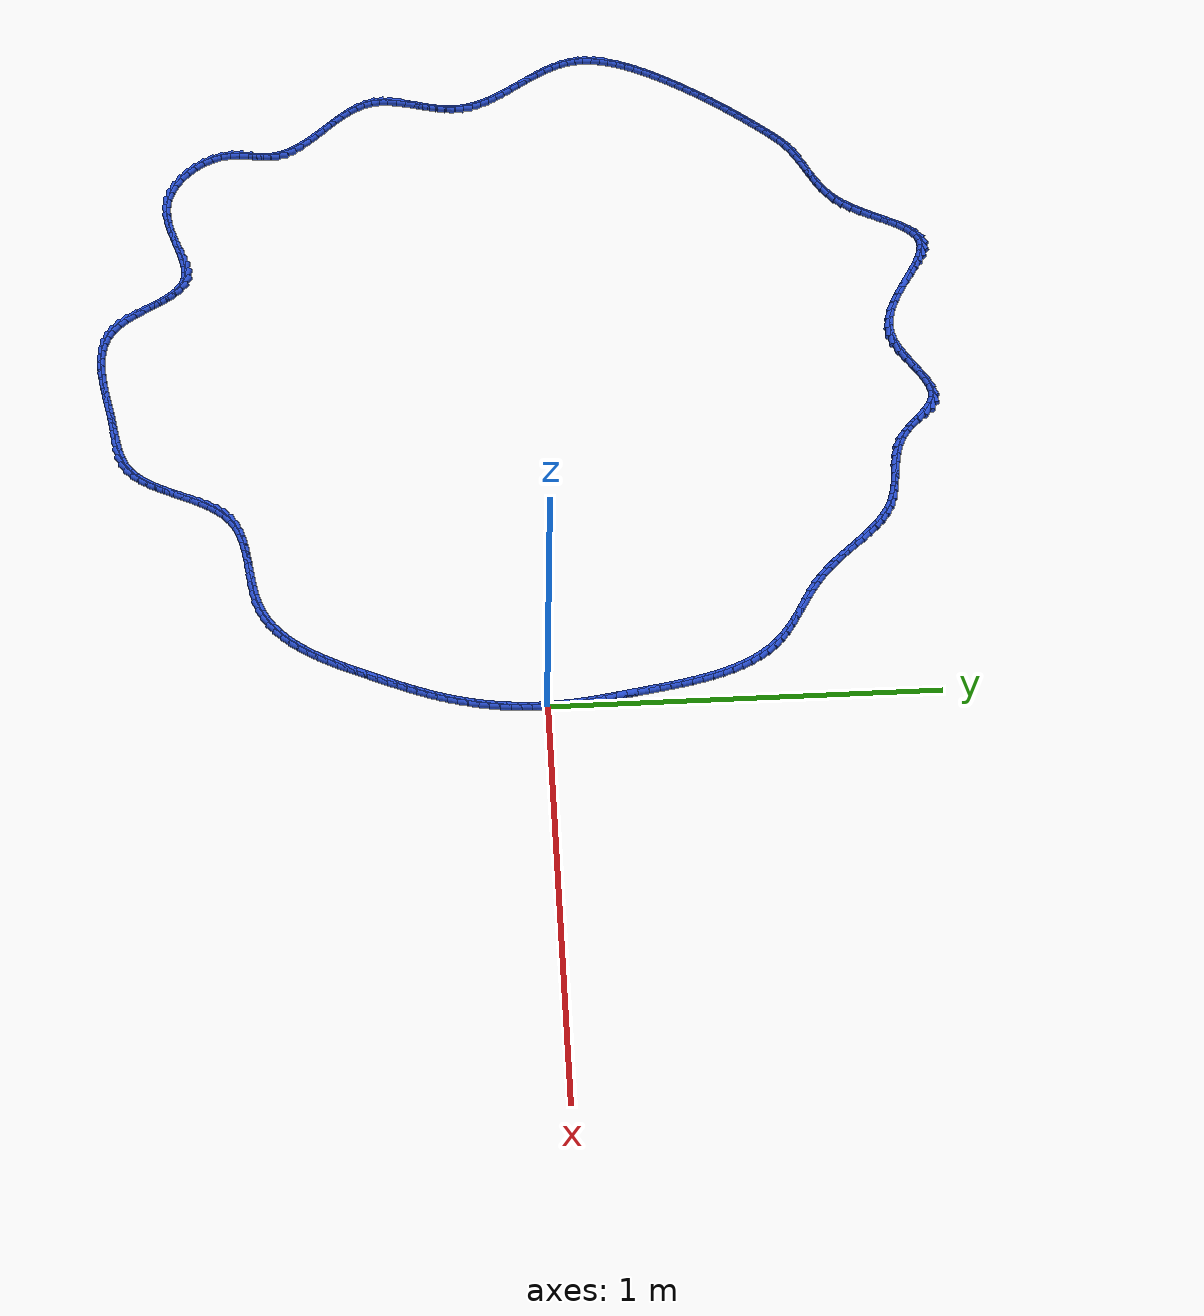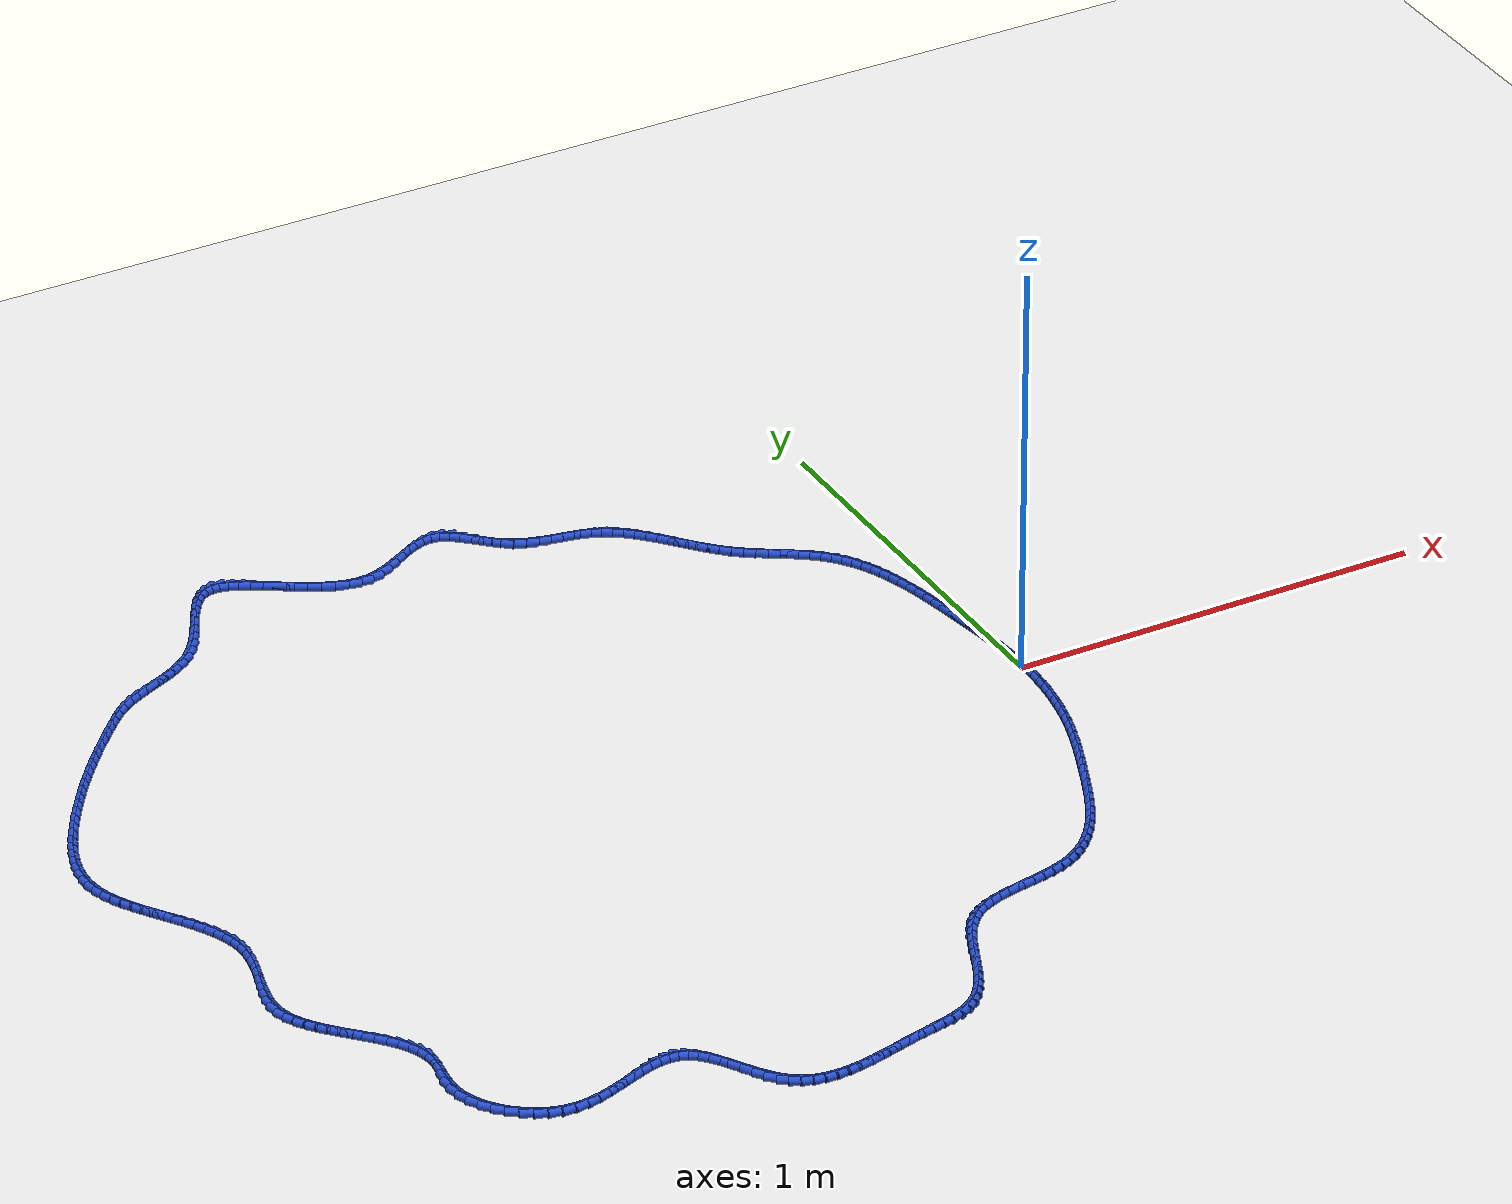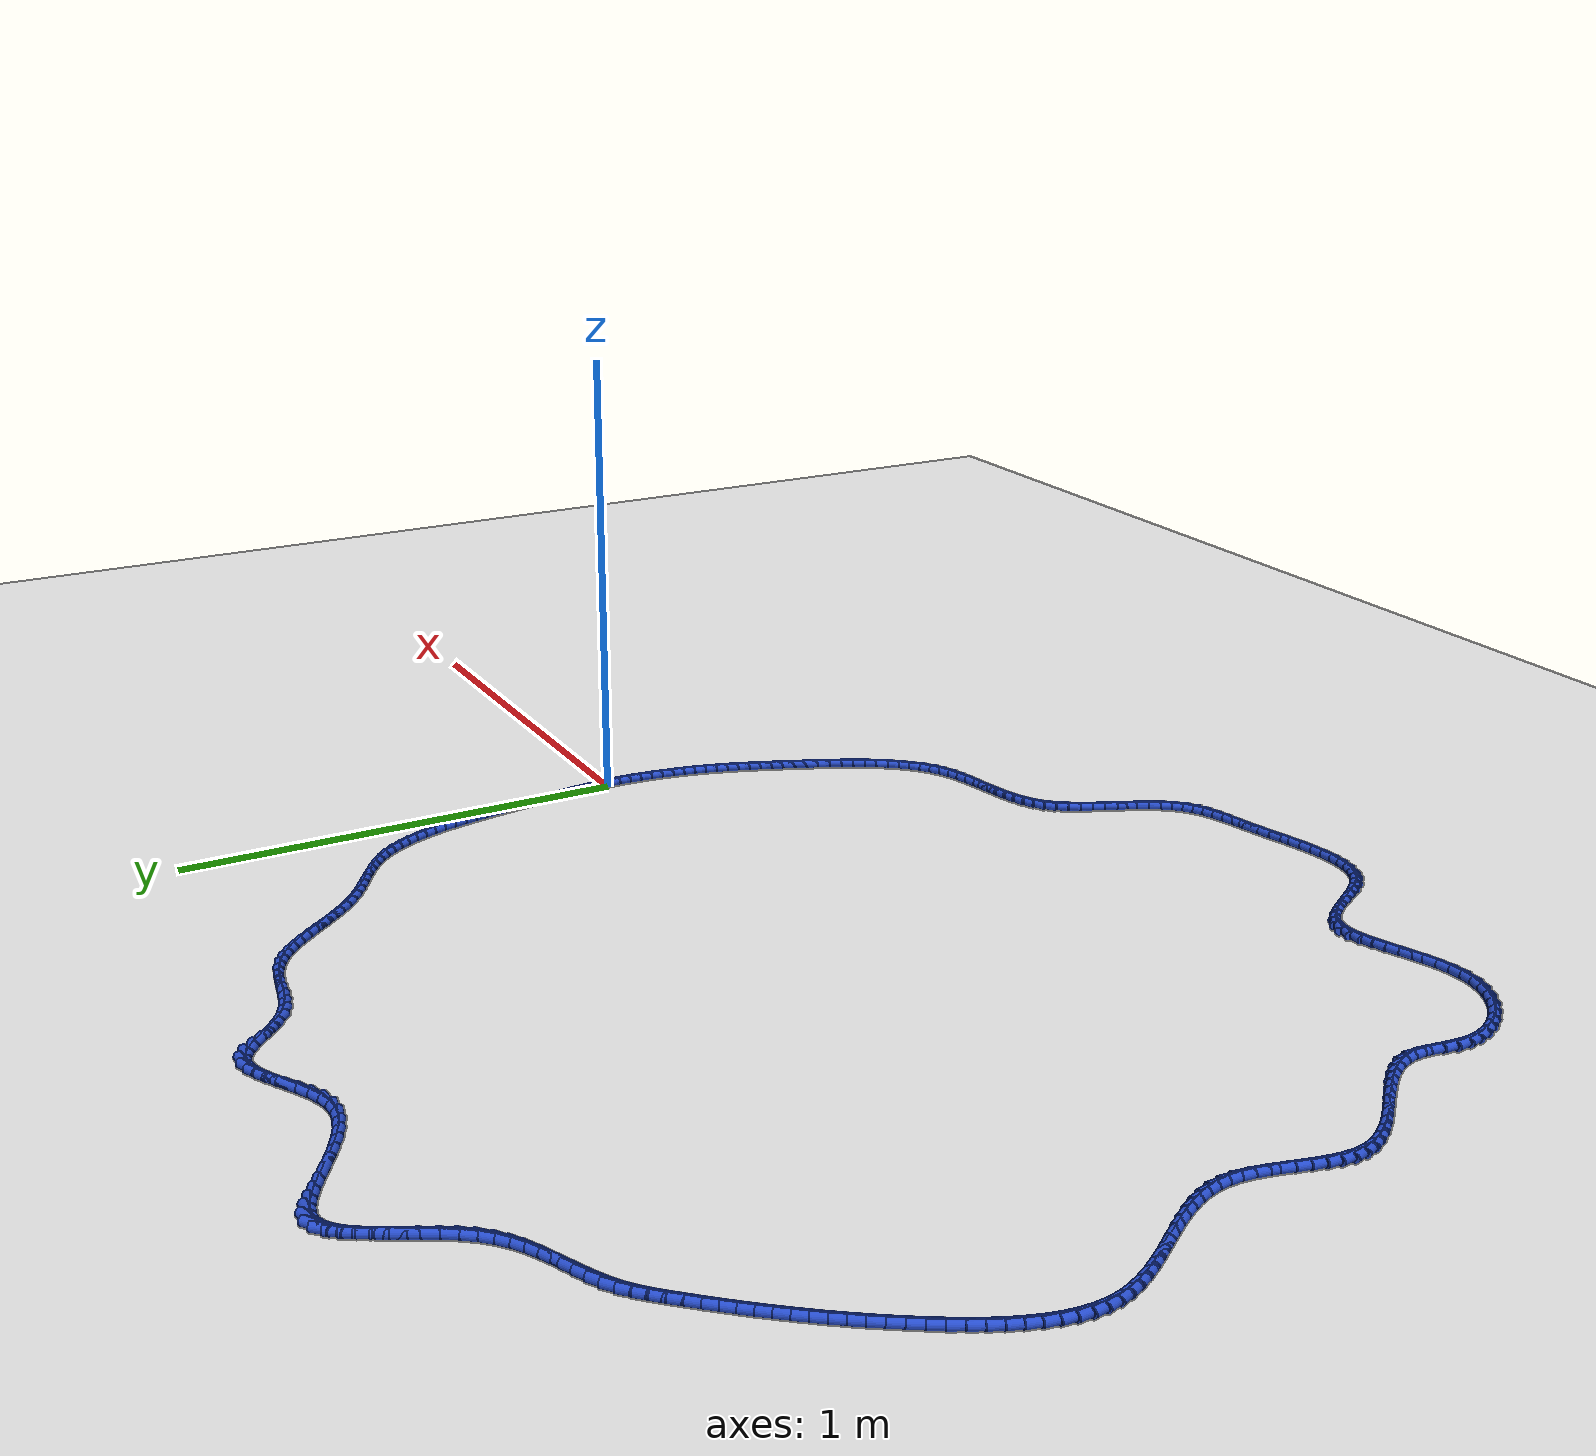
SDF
<sdf version="1.6">
 <world name="default">
  <light name="sun" type="directional">
   <pose>0 0 10 0 -0 0</pose>
   <diffuse>0.8 0.8 0.8 1</diffuse>
   <specular>0.2 0.2 0.2 1</specular>
   <attenuation>
    <range>1000</range>
    <constant>0.9</constant>
    <linear>0.01</linear>
    <quadratic>0.001</quadratic>
   </attenuation>
   <direction>-0.5 0.1 -0.9</direction>
  </light>
  <model name="ground_plane">
   <static>1</static>
   <link name="link">
    <collision name="collision">
     <geometry><plane><normal>0 0 1</normal><size>100 100</size></plane></geometry>
     <surface><friction><ode><mu>100</mu><mu2>50</mu2></ode></friction></surface>
    </collision>
    <visual name="visual">
     <cast_shadows>0</cast_shadows>
     <geometry><plane><normal>0 0 1</normal><size>100 100</size></plane></geometry>
     <material>
      <script><uri>file://media/materials/scripts/gazebo.material</uri><name>Gazebo/WhiteGlow</name></script>
     </material>
    </visual>
   </link>
  </model>
  <gravity>0 0 -9.8</gravity>
  <magnetic_field>6e-06 2.3e-05 -4.2e-05</magnetic_field>
  <atmosphere type="adiabatic"/>
  <physics name="default_physics" default="0" type="ode">
   <max_step_size>0.001</max_step_size>
   <real_time_factor>1</real_time_factor>
   <real_time_update_rate>1000</real_time_update_rate>
  </physics>
  <scene><ambient>0.4 0.4 0.4 1</ambient><background>0.7 0.7 0.7 1</background><shadows>1</shadows></scene>
  <spherical_coordinates>
   <surface_model>EARTH_WGS84</surface_model>
   <latitude_deg>0</latitude_deg>
   <longitude_deg>0</longitude_deg>
   <elevation>0</elevation>
   <heading_deg>0</heading_deg>
  </spherical_coordinates>
  <model name="line">
   <link name="link_0">
    <pose>-1.0408340855860843e-17 -1.3877787807814457e-17 0.01 0 1.57 -1.5336174491078884</pose>
    <collision name="collision">
     <geometry><cylinder><radius>0.01</radius><length>0.08</length></cylinder></geometry>
    </collision>
    <visual name="visual">
     <material>
      <script><name>Gazebo/Blue</name><uri>file://media/materials/scripts/gazebo.material</uri></script>
     </material>
     <geometry><cylinder><radius>0.01</radius><length>0.08</length></cylinder></geometry>
    </visual>
   </link>
   <link name="link_1">
    <pose>-0.000982856391624808 0.02642369952285287 0.01 0 1.57 -1.5039176916772583</pose>
    <collision name="collision">
     <geometry><cylinder><radius>0.01</radius><length>0.08</length></cylinder></geometry>
    </collision>
    <visual name="visual">
     <material>
      <script><name>Gazebo/Blue</name><uri>file://media/materials/scripts/gazebo.material</uri></script>
     </material>
     <geometry><cylinder><radius>0.01</radius><length>0.08</length></cylinder></geometry>
    </visual>
   </link>
   <link name="link_2">
    <pose>-0.002744222687741935 0.05272117790590094 0.01 0 1.57 -1.4781685751957008</pose>
    <collision name="collision">
     <geometry><cylinder><radius>0.01</radius><length>0.08</length></cylinder></geometry>
    </collision>
    <visual name="visual">
     <material>
      <script><name>Gazebo/Blue</name><uri>file://media/materials/scripts/gazebo.material</uri></script>
     </material>
     <geometry><cylinder><radius>0.01</radius><length>0.08</length></cylinder></geometry>
    </visual>
   </link>
   <link name="link_3">
    <pose>-0.005181492058033584 0.07895839978091115 0.01 0 1.57 -1.456576531036775</pose>
    <collision name="collision">
     <geometry><cylinder><radius>0.01</radius><length>0.08</length></cylinder></geometry>
    </collision>
    <visual name="visual">
     <material>
      <script><name>Gazebo/Blue</name><uri>file://media/materials/scripts/gazebo.material</uri></script>
     </material>
     <geometry><cylinder><radius>0.01</radius><length>0.08</length></cylinder></geometry>
    </visual>
   </link>
   <link name="link_4">
    <pose>-0.00819205767218193 0.10520132977965051 0.01 0 1.57 -1.4392664494609209</pose>
    <collision name="collision">
     <geometry><cylinder><radius>0.01</radius><length>0.08</length></cylinder></geometry>
    </collision>
    <visual name="visual">
     <material>
      <script><name>Gazebo/Blue</name><uri>file://media/materials/scripts/gazebo.material</uri></script>
     </material>
     <geometry><cylinder><radius>0.01</radius><length>0.08</length></cylinder></geometry>
    </visual>
   </link>
   <link name="link_5">
    <pose>-0.01167331269986916 0.13151593253388594 0.01 0 1.57 -1.4262903683072554</pose>
    <collision name="collision">
     <geometry><cylinder><radius>0.01</radius><length>0.08</length></cylinder></geometry>
    </collision>
    <visual name="visual">
     <material>
      <script><name>Gazebo/Blue</name><uri>file://media/materials/scripts/gazebo.material</uri></script>
     </material>
     <geometry><cylinder><radius>0.01</radius><length>0.08</length></cylinder></geometry>
    </visual>
   </link>
   <link name="link_6">
    <pose>-0.015522650310777469 0.15796817267538446 0.01 0 1.57 -1.4176370997379664</pose>
    <collision name="collision">
     <geometry><cylinder><radius>0.01</radius><length>0.08</length></cylinder></geometry>
    </collision>
    <visual name="visual">
     <material>
      <script><name>Gazebo/Blue</name><uri>file://media/materials/scripts/gazebo.material</uri></script>
     </material>
     <geometry><cylinder><radius>0.01</radius><length>0.08</length></cylinder></geometry>
    </visual>
   </link>
   <link name="link_7">
    <pose>-0.01963746367458903 0.1846240148359131 0.01 0 1.57 -1.4132415097170756</pose>
    <collision name="collision">
     <geometry><cylinder><radius>0.01</radius><length>0.08</length></cylinder></geometry>
    </collision>
    <visual name="visual">
     <material>
      <script><name>Gazebo/Blue</name><uri>file://media/materials/scripts/gazebo.material</uri></script>
     </material>
     <geometry><cylinder><radius>0.01</radius><length>0.08</length></cylinder></geometry>
    </visual>
   </link>
   <link name="link_8">
    <pose>-0.02391514596098604 0.21154942364723878 0.01 0 1.57 -1.4129508391426517</pose>
    <collision name="collision">
     <geometry><cylinder><radius>0.01</radius><length>0.08</length></cylinder></geometry>
    </collision>
    <visual name="visual">
     <material>
      <script><name>Gazebo/Blue</name><uri>file://media/materials/scripts/gazebo.material</uri></script>
     </material>
     <geometry><cylinder><radius>0.01</radius><length>0.08</length></cylinder></geometry>
    </visual>
   </link>
   <link name="link_9">
    <pose>-0.02825411488879619 0.23880945857655608 0.01 0 1.57 -1.4134061681739547</pose>
    <collision name="collision">
     <geometry><cylinder><radius>0.01</radius><length>0.08</length></cylinder></geometry>
    </collision>
    <visual name="visual">
     <material>
      <script><name>Gazebo/Blue</name><uri>file://media/materials/scripts/gazebo.material</uri></script>
     </material>
     <geometry><cylinder><radius>0.01</radius><length>0.08</length></cylinder></geometry>
    </visual>
   </link>
   <link name="link_10">
    <pose>-0.03263259892591597 0.2663986682103808 0.01 0 1.57 -1.4091634492211198</pose>
    <collision name="collision">
     <geometry><cylinder><radius>0.01</radius><length>0.08</length></cylinder></geometry>
    </collision>
    <visual name="visual">
     <material>
      <script><name>Gazebo/Blue</name><uri>file://media/materials/scripts/gazebo.material</uri></script>
     </material>
     <geometry><cylinder><radius>0.01</radius><length>0.08</length></cylinder></geometry>
    </visual>
   </link>
   <link name="link_11">
    <pose>-0.03716441807337636 0.2941918092710313 0.01 0 1.57 -1.3997590681331178</pose>
    <collision name="collision">
     <geometry><cylinder><radius>0.01</radius><length>0.08</length></cylinder></geometry>
    </collision>
    <visual name="visual">
     <material>
      <script><name>Gazebo/Blue</name><uri>file://media/materials/scripts/gazebo.material</uri></script>
     </material>
     <geometry><cylinder><radius>0.01</radius><length>0.08</length></cylinder></geometry>
    </visual>
   </link>
   <link name="link_12">
    <pose>-0.041976565049787536 0.32205200070109957 0.01 0 1.57 -1.385143365111799</pose>
    <collision name="collision">
     <geometry><cylinder><radius>0.01</radius><length>0.08</length></cylinder></geometry>
    </collision>
    <visual name="visual">
     <material>
      <script><name>Gazebo/Blue</name><uri>file://media/materials/scripts/gazebo.material</uri></script>
     </material>
     <geometry><cylinder><radius>0.01</radius><length>0.08</length></cylinder></geometry>
    </visual>
   </link>
   <link name="link_13">
    <pose>-0.04719603257375975 0.34984236144317804 0.01 0 1.57 -1.3651512273421436</pose>
    <collision name="collision">
     <geometry><cylinder><radius>0.01</radius><length>0.08</length></cylinder></geometry>
    </collision>
    <visual name="visual">
     <material>
      <script><name>Gazebo/Blue</name><uri>file://media/materials/scripts/gazebo.material</uri></script>
     </material>
     <geometry><cylinder><radius>0.01</radius><length>0.08</length></cylinder></geometry>
    </visual>
   </link>
   <link name="link_14">
    <pose>-0.05294981336390316 0.3774260104398588 0.01 0 1.57 -1.3395087243358954</pose>
    <collision name="collision">
     <geometry><cylinder><radius>0.01</radius><length>0.08</length></cylinder></geometry>
    </collision>
    <visual name="visual">
     <material>
      <script><name>Gazebo/Blue</name><uri>file://media/materials/scripts/gazebo.material</uri></script>
     </material>
     <geometry><cylinder><radius>0.01</radius><length>0.08</length></cylinder></geometry>
    </visual>
   </link>
   <link name="link_15">
    <pose>-0.05936490013882802 0.40466606663373406 0.01 0 1.57 -1.3078405323385325</pose>
    <collision name="collision">
     <geometry><cylinder><radius>0.01</radius><length>0.08</length></cylinder></geometry>
    </collision>
    <visual name="visual">
     <material>
      <script><name>Gazebo/Blue</name><uri>file://media/materials/scripts/gazebo.material</uri></script>
     </material>
     <geometry><cylinder><radius>0.01</radius><length>0.08</length></cylinder></geometry>
    </visual>
   </link>
   <link name="link_16">
    <pose>-0.06656828561714451 0.431425648967396 0.01 0 1.57 -1.269681693030669</pose>
    <collision name="collision">
     <geometry><cylinder><radius>0.01</radius><length>0.08</length></cylinder></geometry>
    </collision>
    <visual name="visual">
     <material>
      <script><name>Gazebo/Blue</name><uri>file://media/materials/scripts/gazebo.material</uri></script>
     </material>
     <geometry><cylinder><radius>0.01</radius><length>0.08</length></cylinder></geometry>
    </visual>
   </link>
   <link name="link_17">
    <pose>-0.07468696251746283 0.4575678763834366 0.01 0 1.57 -1.2244987757503798</pose>
    <collision name="collision">
     <geometry><cylinder><radius>0.01</radius><length>0.08</length></cylinder></geometry>
    </collision>
    <visual name="visual">
     <material>
      <script><name>Gazebo/Blue</name><uri>file://media/materials/scripts/gazebo.material</uri></script>
     </material>
     <geometry><cylinder><radius>0.01</radius><length>0.08</length></cylinder></geometry>
    </visual>
   </link>
   <link name="link_18">
    <pose>-0.08384792355839318 0.4829558678244483 0.01 0 1.57 -1.1717273853085721</pose>
    <collision name="collision">
     <geometry><cylinder><radius>0.01</radius><length>0.08</length></cylinder></geometry>
    </collision>
    <visual name="visual">
     <material>
      <script><name>Gazebo/Blue</name><uri>file://media/materials/scripts/gazebo.material</uri></script>
     </material>
     <geometry><cylinder><radius>0.01</radius><length>0.08</length></cylinder></geometry>
    </visual>
   </link>
   <link name="link_19">
    <pose>-0.09417816145854581 0.5074527422330231 0.01 0 1.57 -1.110834590112707</pose>
    <collision name="collision">
     <geometry><cylinder><radius>0.01</radius><length>0.08</length></cylinder></geometry>
    </collision>
    <visual name="visual">
     <material>
      <script><name>Gazebo/Blue</name><uri>file://media/materials/scripts/gazebo.material</uri></script>
     </material>
     <geometry><cylinder><radius>0.01</radius><length>0.08</length></cylinder></geometry>
    </visual>
   </link>
   <link name="link_20">
    <pose>-0.10580466893653086 0.5309216185517531 0.01 0 1.57 -1.041414743018342</pose>
    <collision name="collision">
     <geometry><cylinder><radius>0.01</radius><length>0.08</length></cylinder></geometry>
    </collision>
    <visual name="visual">
     <material>
      <script><name>Gazebo/Blue</name><uri>file://media/materials/scripts/gazebo.material</uri></script>
     </material>
     <geometry><cylinder><radius>0.01</radius><length>0.08</length></cylinder></geometry>
    </visual>
   </link>
   <link name="link_21">
    <pose>-0.11885443871095866 0.553225615723231 0.01 0 1.57 -0.96332255323922</pose>
    <collision name="collision">
     <geometry><cylinder><radius>0.01</radius><length>0.08</length></cylinder></geometry>
    </collision>
    <visual name="visual">
     <material>
      <script><name>Gazebo/Blue</name><uri>file://media/materials/scripts/gazebo.material</uri></script>
     </material>
     <geometry><cylinder><radius>0.01</radius><length>0.08</length></cylinder></geometry>
    </visual>
   </link>
   <link name="link_22">
    <pose>-0.1334544635004393 0.5742278526900485 0.01 0 1.57 -0.8768345508542901</pose>
    <collision name="collision">
     <geometry><cylinder><radius>0.01</radius><length>0.08</length></cylinder></geometry>
    </collision>
    <visual name="visual">
     <material>
      <script><name>Gazebo/Blue</name><uri>file://media/materials/scripts/gazebo.material</uri></script>
     </material>
     <geometry><cylinder><radius>0.01</radius><length>0.08</length></cylinder></geometry>
    </visual>
   </link>
   <link name="link_23">
    <pose>-0.14973173602358297 0.5937914483947977 0.01 0 1.57 -0.7833844180487131</pose>
    <collision name="collision">
     <geometry><cylinder><radius>0.01</radius><length>0.08</length></cylinder></geometry>
    </collision>
    <visual name="visual">
     <material>
      <script><name>Gazebo/Blue</name><uri>file://media/materials/scripts/gazebo.material</uri></script>
     </material>
     <geometry><cylinder><radius>0.01</radius><length>0.08</length></cylinder></geometry>
    </visual>
   </link>
   <link name="link_24">
    <pose>-0.1678031843455397 0.6117902602998103 0.01 0 1.57 -0.6978880449947527</pose>
    <collision name="collision">
     <geometry><cylinder><radius>0.01</radius><length>0.08</length></cylinder></geometry>
    </collision>
    <visual name="visual">
     <material>
      <script><name>Gazebo/Blue</name><uri>file://media/materials/scripts/gazebo.material</uri></script>
     </material>
     <geometry><cylinder><radius>0.01</radius><length>0.08</length></cylinder></geometry>
    </visual>
   </link>
   <link name="link_25">
    <pose>-0.1875489805146812 0.6283507535870546 0.01 0 1.57 -0.6345981497628191</pose>
    <collision name="collision">
     <geometry><cylinder><radius>0.01</radius><length>0.08</length></cylinder></geometry>
    </collision>
    <visual name="visual">
     <material>
      <script><name>Gazebo/Blue</name><uri>file://media/materials/scripts/gazebo.material</uri></script>
     </material>
     <geometry><cylinder><radius>0.01</radius><length>0.08</length></cylinder></geometry>
    </visual>
   </link>
   <link name="link_26">
    <pose>-0.20860957581595085 0.6438551644056875 0.01 0 1.57 -0.5933884863013864</pose>
    <collision name="collision">
     <geometry><cylinder><radius>0.01</radius><length>0.08</length></cylinder></geometry>
    </collision>
    <visual name="visual">
     <material>
      <script><name>Gazebo/Blue</name><uri>file://media/materials/scripts/gazebo.material</uri></script>
     </material>
     <geometry><cylinder><radius>0.01</radius><length>0.08</length></cylinder></geometry>
    </visual>
   </link>
   <link name="link_27">
    <pose>-0.23061476390271546 0.6586971001048308 0.01 0 1.57 -0.5731412592341645</pose>
    <collision name="collision">
     <geometry><cylinder><radius>0.01</radius><length>0.08</length></cylinder></geometry>
    </collision>
    <visual name="visual">
     <material>
      <script><name>Gazebo/Blue</name><uri>file://media/materials/scripts/gazebo.material</uri></script>
     </material>
     <geometry><cylinder><radius>0.01</radius><length>0.08</length></cylinder></geometry>
    </visual>
   </link>
   <link name="link_28">
    <pose>-0.25319433842834144 0.6732701680336054 0.01 0 1.57 -0.5729230941366822</pose>
    <collision name="collision">
     <geometry><cylinder><radius>0.01</radius><length>0.08</length></cylinder></geometry>
    </collision>
    <visual name="visual">
     <material>
      <script><name>Gazebo/Blue</name><uri>file://media/materials/scripts/gazebo.material</uri></script>
     </material>
     <geometry><cylinder><radius>0.01</radius><length>0.08</length></cylinder></geometry>
    </visual>
   </link>
   <link name="link_29">
    <pose>-0.27597809304619525 0.6879679755411329 0.01 0 1.57 -0.5922046900586779</pose>
    <collision name="collision">
     <geometry><cylinder><radius>0.01</radius><length>0.08</length></cylinder></geometry>
    </collision>
    <visual name="visual">
     <material>
      <script><name>Gazebo/Blue</name><uri>file://media/materials/scripts/gazebo.material</uri></script>
     </material>
     <geometry><cylinder><radius>0.01</radius><length>0.08</length></cylinder></geometry>
    </visual>
   </link>
   <link name="link_30">
    <pose>-0.29859582140964364 0.7031841299765341 0.01 0 1.57 -0.6308322780184294</pose>
    <collision name="collision">
     <geometry><cylinder><radius>0.01</radius><length>0.08</length></cylinder></geometry>
    </collision>
    <visual name="visual">
     <material>
      <script><name>Gazebo/Blue</name><uri>file://media/materials/scripts/gazebo.material</uri></script>
     </material>
     <geometry><cylinder><radius>0.01</radius><length>0.08</length></cylinder></geometry>
    </visual>
   </link>
   <link name="link_31">
    <pose>-0.3206773171720529 0.7193122386889302 0.01 0 1.57 -0.6887738274015756</pose>
    <collision name="collision">
     <geometry><cylinder><radius>0.01</radius><length>0.08</length></cylinder></geometry>
    </collision>
    <visual name="visual">
     <material>
      <script><name>Gazebo/Blue</name><uri>file://media/materials/scripts/gazebo.material</uri></script>
     </material>
     <geometry><cylinder><radius>0.01</radius><length>0.08</length></cylinder></geometry>
    </visual>
   </link>
   <link name="link_32">
    <pose>-0.3418527236576344 0.736745458982502 0.01 0 1.57 -0.7565763140817067</pose>
    <collision name="collision">
     <geometry><cylinder><radius>0.01</radius><length>0.08</length></cylinder></geometry>
    </collision>
    <visual name="visual">
     <material>
      <script><name>Gazebo/Blue</name><uri>file://media/materials/scripts/gazebo.material</uri></script>
     </material>
     <geometry><cylinder><radius>0.01</radius><length>0.08</length></cylinder></geometry>
    </visual>
   </link>
   <link name="link_33">
    <pose>-0.361907841367163 0.7556766091115201 0.01 0 1.57 -0.8105428518303144</pose>
    <collision name="collision">
     <geometry><cylinder><radius>0.01</radius><length>0.08</length></cylinder></geometry>
    </collision>
    <visual name="visual">
     <material>
      <script><name>Gazebo/Blue</name><uri>file://media/materials/scripts/gazebo.material</uri></script>
     </material>
     <geometry><cylinder><radius>0.01</radius><length>0.08</length></cylinder></geometry>
    </visual>
   </link>
   <link name="link_34">
    <pose>-0.38102841428922724 0.775783758828869 0.01 0 1.57 -0.8474976606497334</pose>
    <collision name="collision">
     <geometry><cylinder><radius>0.01</radius><length>0.08</length></cylinder></geometry>
    </collision>
    <visual name="visual">
     <material>
      <script><name>Gazebo/Blue</name><uri>file://media/materials/scripts/gazebo.material</uri></script>
     </material>
     <geometry><cylinder><radius>0.01</radius><length>0.08</length></cylinder></geometry>
    </visual>
   </link>
   <link name="link_35">
    <pose>-0.39946353166613874 0.7966634491829597 0.01 0 1.57 -0.8680179677769879</pose>
    <collision name="collision">
     <geometry><cylinder><radius>0.01</radius><length>0.08</length></cylinder></geometry>
    </collision>
    <visual name="visual">
     <material>
      <script><name>Gazebo/Blue</name><uri>file://media/materials/scripts/gazebo.material</uri></script>
     </material>
     <geometry><cylinder><radius>0.01</radius><length>0.08</length></cylinder></geometry>
    </visual>
   </link>
   <link name="link_36">
    <pose>-0.4174622827402099 0.8179122212222042 0.01 0 1.57 -0.8723747149108502</pose>
    <collision name="collision">
     <geometry><cylinder><radius>0.01</radius><length>0.08</length></cylinder></geometry>
    </collision>
    <visual name="visual">
     <material>
      <script><name>Gazebo/Blue</name><uri>file://media/materials/scripts/gazebo.material</uri></script>
     </material>
     <geometry><cylinder><radius>0.01</radius><length>0.08</length></cylinder></geometry>
    </visual>
   </link>
   <link name="link_37">
    <pose>-0.43527375675375213 0.8391266159950129 0.01 0 1.57 -0.8603746636498303</pose>
    <collision name="collision">
     <geometry><cylinder><radius>0.01</radius><length>0.08</length></cylinder></geometry>
    </collision>
    <visual name="visual">
     <material>
      <script><name>Gazebo/Blue</name><uri>file://media/materials/scripts/gazebo.material</uri></script>
     </material>
     <geometry><cylinder><radius>0.01</radius><length>0.08</length></cylinder></geometry>
    </visual>
   </link>
   <link name="link_38">
    <pose>-0.45314704294907737 0.8599031745497976 0.01 0 1.57 -0.8313024350996501</pose>
    <collision name="collision">
     <geometry><cylinder><radius>0.01</radius><length>0.08</length></cylinder></geometry>
    </collision>
    <visual name="visual">
     <material>
      <script><name>Gazebo/Blue</name><uri>file://media/materials/scripts/gazebo.material</uri></script>
     </material>
     <geometry><cylinder><radius>0.01</radius><length>0.08</length></cylinder></geometry>
    </visual>
   </link>
   <link name="link_39">
    <pose>-0.4713312305684973 0.8798384379349692 0.01 0 1.57 -0.7839644934886402</pose>
    <collision name="collision">
     <geometry><cylinder><radius>0.01</radius><length>0.08</length></cylinder></geometry>
    </collision>
    <visual name="visual">
     <material>
      <script><name>Gazebo/Blue</name><uri>file://media/materials/scripts/gazebo.material</uri></script>
     </material>
     <geometry><cylinder><radius>0.01</radius><length>0.08</length></cylinder></geometry>
    </visual>
   </link>
   <link name="link_40">
    <pose>-0.49007540885432366 0.8985289471989392 0.01 0 1.57 -0.7168916817004928</pose>
    <collision name="collision">
     <geometry><cylinder><radius>0.01</radius><length>0.08</length></cylinder></geometry>
    </collision>
    <visual name="visual">
     <material>
      <script><name>Gazebo/Blue</name><uri>file://media/materials/scripts/gazebo.material</uri></script>
     </material>
     <geometry><cylinder><radius>0.01</radius><length>0.08</length></cylinder></geometry>
    </visual>
   </link>
   <link name="link_41">
    <pose>-0.5096286670488686 0.9155712433901184 0.01 0 1.57 -0.6288119998419277</pose>
    <collision name="collision">
     <geometry><cylinder><radius>0.01</radius><length>0.08</length></cylinder></geometry>
    </collision>
    <visual name="visual">
     <material>
      <script><name>Gazebo/Blue</name><uri>file://media/materials/scripts/gazebo.material</uri></script>
     </material>
     <geometry><cylinder><radius>0.01</radius><length>0.08</length></cylinder></geometry>
    </visual>
   </link>
   <link name="link_42">
    <pose>-0.5302400943944439 0.9305618675569188 0.01 0 1.57 -0.5195081930052509</pose>
    <collision name="collision">
     <geometry><cylinder><radius>0.01</radius><length>0.08</length></cylinder></geometry>
    </collision>
    <visual name="visual">
     <material>
      <script><name>Gazebo/Blue</name><uri>file://media/materials/scripts/gazebo.material</uri></script>
     </material>
     <geometry><cylinder><radius>0.01</radius><length>0.08</length></cylinder></geometry>
    </visual>
   </link>
   <link name="link_43">
    <pose>-0.5521587801333612 0.9430973607477511 0.01 0 1.57 -0.3928359924762376</pose>
    <collision name="collision">
     <geometry><cylinder><radius>0.01</radius><length>0.08</length></cylinder></geometry>
    </collision>
    <visual name="visual">
     <material>
      <script><name>Gazebo/Blue</name><uri>file://media/materials/scripts/gazebo.material</uri></script>
     </material>
     <geometry><cylinder><radius>0.01</radius><length>0.08</length></cylinder></geometry>
    </visual>
   </link>
   <link name="link_44">
    <pose>-0.5756129374965655 0.9528161531042059 0.01 0 1.57 -0.2833658775620878</pose>
    <collision name="collision">
     <geometry><cylinder><radius>0.01</radius><length>0.08</length></cylinder></geometry>
    </collision>
    <visual name="visual">
     <material>
      <script><name>Gazebo/Blue</name><uri>file://media/materials/scripts/gazebo.material</uri></script>
     </material>
     <geometry><cylinder><radius>0.01</radius><length>0.08</length></cylinder></geometry>
    </visual>
   </link>
   <link name="link_45">
    <pose>-0.600481324925978 0.9600578788418842 0.01 0 1.57 -0.21629301591343814</pose>
    <collision name="collision">
     <geometry><cylinder><radius>0.01</radius><length>0.08</length></cylinder></geometry>
    </collision>
    <visual name="visual">
     <material>
      <script><name>Gazebo/Blue</name><uri>file://media/materials/scripts/gazebo.material</uri></script>
     </material>
     <geometry><cylinder><radius>0.01</radius><length>0.08</length></cylinder></geometry>
    </visual>
   </link>
   <link name="link_46">
    <pose>-0.6263533624763928 0.9657427487264656 0.01 0 1.57 -0.1891844893317673</pose>
    <collision name="collision">
     <geometry><cylinder><radius>0.01</radius><length>0.08</length></cylinder></geometry>
    </collision>
    <visual name="visual">
     <material>
      <script><name>Gazebo/Blue</name><uri>file://media/materials/scripts/gazebo.material</uri></script>
     </material>
     <geometry><cylinder><radius>0.01</radius><length>0.08</length></cylinder></geometry>
    </visual>
   </link>
   <link name="link_47">
    <pose>-0.6528097519474474 0.9708084672774063 0.01 0 1.57 -0.19956114438215225</pose>
    <collision name="collision">
     <geometry><cylinder><radius>0.01</radius><length>0.08</length></cylinder></geometry>
    </collision>
    <visual name="visual">
     <material>
      <script><name>Gazebo/Blue</name><uri>file://media/materials/scripts/gazebo.material</uri></script>
     </material>
     <geometry><cylinder><radius>0.01</radius><length>0.08</length></cylinder></geometry>
    </visual>
   </link>
   <link name="link_48">
    <pose>-0.6794311951387783 0.9761927390141613 0.01 0 1.57 -0.24671731298215</pose>
    <collision name="collision">
     <geometry><cylinder><radius>0.01</radius><length>0.08</length></cylinder></geometry>
    </collision>
    <visual name="visual">
     <material>
      <script><name>Gazebo/Blue</name><uri>file://media/materials/scripts/gazebo.material</uri></script>
     </material>
     <geometry><cylinder><radius>0.01</radius><length>0.08</length></cylinder></geometry>
    </visual>
   </link>
   <link name="link_49">
    <pose>-0.7057983938500223 0.982833268456186 0.01 0 1.57 -0.3311760406851753</pose>
    <collision name="collision">
     <geometry><cylinder><radius>0.01</radius><length>0.08</length></cylinder></geometry>
    </collision>
    <visual name="visual">
     <material>
      <script><name>Gazebo/Blue</name><uri>file://media/materials/scripts/gazebo.material</uri></script>
     </material>
     <geometry><cylinder><radius>0.01</radius><length>0.08</length></cylinder></geometry>
    </visual>
   </link>
   <link name="link_50">
    <pose>-0.7314920498808166 0.9916677601229367 0.01 0 1.57 -0.4527191165925859</pose>
    <collision name="collision">
     <geometry><cylinder><radius>0.01</radius><length>0.08</length></cylinder></geometry>
    </collision>
    <visual name="visual">
     <material>
      <script><name>Gazebo/Blue</name><uri>file://media/materials/scripts/gazebo.material</uri></script>
     </material>
     <geometry><cylinder><radius>0.01</radius><length>0.08</length></cylinder></geometry>
    </visual>
   </link>
   <link name="link_51">
    <pose>-0.7560928650307976 1.0036339185338679 0.01 0 1.57 -0.6033936116225007</pose>
    <collision name="collision">
     <geometry><cylinder><radius>0.01</radius><length>0.08</length></cylinder></geometry>
    </collision>
    <visual name="visual">
     <material>
      <script><name>Gazebo/Blue</name><uri>file://media/materials/scripts/gazebo.material</uri></script>
     </material>
     <geometry><cylinder><radius>0.01</radius><length>0.08</length></cylinder></geometry>
    </visual>
   </link>
   <link name="link_52">
    <pose>-0.7792114746429604 1.0195656549795429 0.01 0 1.57 -0.7210777675342803</pose>
    <collision name="collision">
     <geometry><cylinder><radius>0.01</radius><length>0.08</length></cylinder></geometry>
    </collision>
    <visual name="visual">
     <material>
      <script><name>Gazebo/Blue</name><uri>file://media/materials/scripts/gazebo.material</uri></script>
     </material>
     <geometry><cylinder><radius>0.01</radius><length>0.08</length></cylinder></geometry>
    </visual>
   </link>
   <link name="link_53">
    <pose>-0.800931448298232 1.0386570023364612 0.01 0 1.57 -0.7696232735204793</pose>
    <collision name="collision">
     <geometry><cylinder><radius>0.01</radius><length>0.08</length></cylinder></geometry>
    </collision>
    <visual name="visual">
     <material>
      <script><name>Gazebo/Blue</name><uri>file://media/materials/scripts/gazebo.material</uri></script>
     </material>
     <geometry><cylinder><radius>0.01</radius><length>0.08</length></cylinder></geometry>
    </visual>
   </link>
   <link name="link_54">
    <pose>-0.8217136684562714 1.0587936778728324 0.01 0 1.57 -0.752763194397208</pose>
    <collision name="collision">
     <geometry><cylinder><radius>0.01</radius><length>0.08</length></cylinder></geometry>
    </collision>
    <visual name="visual">
     <material>
      <script><name>Gazebo/Blue</name><uri>file://media/materials/scripts/gazebo.material</uri></script>
     </material>
     <geometry><cylinder><radius>0.01</radius><length>0.08</length></cylinder></geometry>
    </visual>
   </link>
   <link name="link_55">
    <pose>-0.8420295204466621 1.077824980623012 0.01 0 1.57 -0.660125985846758</pose>
    <collision name="collision">
     <geometry><cylinder><radius>0.01</radius><length>0.08</length></cylinder></geometry>
    </collision>
    <visual name="visual">
     <material>
      <script><name>Gazebo/Blue</name><uri>file://media/materials/scripts/gazebo.material</uri></script>
     </material>
     <geometry><cylinder><radius>0.01</radius><length>0.08</length></cylinder></geometry>
    </visual>
   </link>
   <link name="link_56">
    <pose>-0.8623503895989879 1.0936002096213562 0.01 0 1.57 -0.46248595440453766</pose>
    <collision name="collision">
     <geometry><cylinder><radius>0.01</radius><length>0.08</length></cylinder></geometry>
    </collision>
    <visual name="visual">
     <material>
      <script><name>Gazebo/Blue</name><uri>file://media/materials/scripts/gazebo.material</uri></script>
     </material>
     <geometry><cylinder><radius>0.01</radius><length>0.08</length></cylinder></geometry>
    </visual>
   </link>
   <link name="link_57">
    <pose>-0.8831476612428316 1.1039686639022213 0.01 0 1.57 -0.14202022993658955</pose>
    <collision name="collision">
     <geometry><cylinder><radius>0.01</radius><length>0.08</length></cylinder></geometry>
    </collision>
    <visual name="visual">
     <material>
      <script><name>Gazebo/Blue</name><uri>file://media/materials/scripts/gazebo.material</uri></script>
     </material>
     <geometry><cylinder><radius>0.01</radius><length>0.08</length></cylinder></geometry>
    </visual>
   </link>
   <link name="link_58">
    <pose>-0.9048495323779722 1.1070716589442244 0.01 0 1.57 0.16095837502814797</pose>
    <collision name="collision">
     <geometry><cylinder><radius>0.01</radius><length>0.08</length></cylinder></geometry>
    </collision>
    <visual name="visual">
     <material>
      <script><name>Gazebo/Blue</name><uri>file://media/materials/scripts/gazebo.material</uri></script>
     </material>
     <geometry><cylinder><radius>0.01</radius><length>0.08</length></cylinder></geometry>
    </visual>
   </link>
   <link name="link_59">
    <pose>-0.927538520901255 1.1033878078929253 0.01 0 1.57 0.35961795064695906</pose>
    <collision name="collision">
     <geometry><cylinder><radius>0.01</radius><length>0.08</length></cylinder></geometry>
    </collision>
    <visual name="visual">
     <material>
      <script><name>Gazebo/Blue</name><uri>file://media/materials/scripts/gazebo.material</uri></script>
     </material>
     <geometry><cylinder><radius>0.01</radius><length>0.08</length></cylinder></geometry>
    </visual>
   </link>
   <link name="link_60">
    <pose>-0.9511312012778204 1.0945177448447618 0.01 0 1.57 0.47156598986149795</pose>
    <collision name="collision">
     <geometry><cylinder><radius>0.01</radius><length>0.08</length></cylinder></geometry>
    </collision>
    <visual name="visual">
     <material>
      <script><name>Gazebo/Blue</name><uri>file://media/materials/scripts/gazebo.material</uri></script>
     </material>
     <geometry><cylinder><radius>0.01</radius><length>0.08</length></cylinder></geometry>
    </visual>
   </link>
   <link name="link_61">
    <pose>-0.9755430981094085 1.082069202512354 0.01 0 1.57 0.5206371930552571</pose>
    <collision name="collision">
     <geometry><cylinder><radius>0.01</radius><length>0.08</length></cylinder></geometry>
    </collision>
    <visual name="visual">
     <material>
      <script><name>Gazebo/Blue</name><uri>file://media/materials/scripts/gazebo.material</uri></script>
     </material>
     <geometry><cylinder><radius>0.01</radius><length>0.08</length></cylinder></geometry>
    </visual>
   </link>
   <link name="link_62">
    <pose>-1.0006897359977607 1.0676499136083235 0.01 0 1.57 0.5203496851456962</pose>
    <collision name="collision">
     <geometry><cylinder><radius>0.01</radius><length>0.08</length></cylinder></geometry>
    </collision>
    <visual name="visual">
     <material>
      <script><name>Gazebo/Blue</name><uri>file://media/materials/scripts/gazebo.material</uri></script>
     </material>
     <geometry><cylinder><radius>0.01</radius><length>0.08</length></cylinder></geometry>
    </visual>
   </link>
   <link name="link_63">
    <pose>-1.0264866395446173 1.0528676108452903 0.01 0 1.57 0.47439941413155706</pose>
    <collision name="collision">
     <geometry><cylinder><radius>0.01</radius><length>0.08</length></cylinder></geometry>
    </collision>
    <visual name="visual">
     <material>
      <script><name>Gazebo/Blue</name><uri>file://media/materials/scripts/gazebo.material</uri></script>
     </material>
     <geometry><cylinder><radius>0.01</radius><length>0.08</length></cylinder></geometry>
    </visual>
   </link>
   <link name="link_64">
    <pose>-1.052849333351719 1.0393300269358752 0.01 0 1.57 0.3788201835636291</pose>
    <collision name="collision">
     <geometry><cylinder><radius>0.01</radius><length>0.08</length></cylinder></geometry>
    </collision>
    <visual name="visual">
     <material>
      <script><name>Gazebo/Blue</name><uri>file://media/materials/scripts/gazebo.material</uri></script>
     </material>
     <geometry><cylinder><radius>0.01</radius><length>0.08</length></cylinder></geometry>
    </visual>
   </link>
   <link name="link_65">
    <pose>-1.0796933420208068 1.0286448945926994 0.01 0 1.57 0.22465773814397805</pose>
    <collision name="collision">
     <geometry><cylinder><radius>0.01</radius><length>0.08</length></cylinder></geometry>
    </collision>
    <visual name="visual">
     <material>
      <script><name>Gazebo/Blue</name><uri>file://media/materials/scripts/gazebo.material</uri></script>
     </material>
     <geometry><cylinder><radius>0.01</radius><length>0.08</length></cylinder></geometry>
    </visual>
   </link>
   <link name="link_66">
    <pose>-1.1069341901536212 1.022419946528383 0.01 0 1.57 0.02020815254820684</pose>
    <collision name="collision">
     <geometry><cylinder><radius>0.01</radius><length>0.08</length></cylinder></geometry>
    </collision>
    <visual name="visual">
     <material>
      <script><name>Gazebo/Blue</name><uri>file://media/materials/scripts/gazebo.material</uri></script>
     </material>
     <geometry><cylinder><radius>0.01</radius><length>0.08</length></cylinder></geometry>
    </visual>
   </link>
   <link name="link_67">
    <pose>-1.1344769636904963 1.0218632821821856 0.01 0 1.57 -0.16537096222450542</pose>
    <collision name="collision">
     <geometry><cylinder><radius>0.01</radius><length>0.08</length></cylinder></geometry>
    </collision>
    <visual name="visual">
     <material>
      <script><name>Gazebo/Blue</name><uri>file://media/materials/scripts/gazebo.material</uri></script>
     </material>
     <geometry><cylinder><radius>0.01</radius><length>0.08</length></cylinder></geometry>
    </visual>
   </link>
   <link name="link_68">
    <pose>-1.1621824530618348 1.0264871935578272 0.01 0 1.57 -0.3096220203757581</pose>
    <collision name="collision">
     <geometry><cylinder><radius>0.01</radius><length>0.08</length></cylinder></geometry>
    </collision>
    <visual name="visual">
     <material>
      <script><name>Gazebo/Blue</name><uri>file://media/materials/scripts/gazebo.material</uri></script>
     </material>
     <geometry><cylinder><radius>0.01</radius><length>0.08</length></cylinder></geometry>
    </visual>
   </link>
   <link name="link_69">
    <pose>-1.189899701421498 1.0353542404190064 0.01 0 1.57 -0.4156727398980598</pose>
    <collision name="collision">
     <geometry><cylinder><radius>0.01</radius><length>0.08</length></cylinder></geometry>
    </collision>
    <visual name="visual">
     <material>
      <script><name>Gazebo/Blue</name><uri>file://media/materials/scripts/gazebo.material</uri></script>
     </material>
     <geometry><cylinder><radius>0.01</radius><length>0.08</length></cylinder></geometry>
    </visual>
   </link>
   <link name="link_70">
    <pose>-1.2174777518388087 1.0475269792929782 0.01 0 1.57 -0.48959899951528796</pose>
    <collision name="collision">
     <geometry><cylinder><radius>0.01</radius><length>0.08</length></cylinder></geometry>
    </collision>
    <visual name="visual">
     <material>
      <script><name>Gazebo/Blue</name><uri>file://media/materials/scripts/gazebo.material</uri></script>
     </material>
     <geometry><cylinder><radius>0.01</radius><length>0.08</length></cylinder></geometry>
    </visual>
   </link>
   <link name="link_71">
    <pose>-1.2447656473830915 1.062067966706999 0.01 0 1.57 -0.5366786917627356</pose>
    <collision name="collision">
     <geometry><cylinder><radius>0.01</radius><length>0.08</length></cylinder></geometry>
    </collision>
    <visual name="visual">
     <material>
      <script><name>Gazebo/Blue</name><uri>file://media/materials/scripts/gazebo.material</uri></script>
     </material>
     <geometry><cylinder><radius>0.01</radius><length>0.08</length></cylinder></geometry>
    </visual>
   </link>
   <link name="link_72">
    <pose>-1.2716124311236696 1.078039759188326 0.01 0 1.57 -0.5601304819937649</pose>
    <collision name="collision">
     <geometry><cylinder><radius>0.01</radius><length>0.08</length></cylinder></geometry>
    </collision>
    <visual name="visual">
     <material>
      <script><name>Gazebo/Blue</name><uri>file://media/materials/scripts/gazebo.material</uri></script>
     </material>
     <geometry><cylinder><radius>0.01</radius><length>0.08</length></cylinder></geometry>
    </visual>
   </link>
   <link name="link_73">
    <pose>-1.2978671461298668 1.0945049132642144 0.01 0 1.57 -0.5607461568363896</pose>
    <collision name="collision">
     <geometry><cylinder><radius>0.01</radius><length>0.08</length></cylinder></geometry>
    </collision>
    <visual name="visual">
     <material>
      <script><name>Gazebo/Blue</name><uri>file://media/materials/scripts/gazebo.material</uri></script>
     </material>
     <geometry><cylinder><radius>0.01</radius><length>0.08</length></cylinder></geometry>
    </visual>
   </link>
   <link name="link_74">
    <pose>-1.323378835471006 1.110525985461921 0.01 0 1.57 -0.5364952219221905</pose>
    <collision name="collision">
     <geometry><cylinder><radius>0.01</radius><length>0.08</length></cylinder></geometry>
    </collision>
    <visual name="visual">
     <material>
      <script><name>Gazebo/Blue</name><uri>file://media/materials/scripts/gazebo.material</uri></script>
     </material>
     <geometry><cylinder><radius>0.01</radius><length>0.08</length></cylinder></geometry>
    </visual>
   </link>
   <link name="link_75">
    <pose>-1.347996542216412 1.1251655323087018 0.01 0 1.57 -0.4816120235274585</pose>
    <collision name="collision">
     <geometry><cylinder><radius>0.01</radius><length>0.08</length></cylinder></geometry>
    </collision>
    <visual name="visual">
     <material>
      <script><name>Gazebo/Blue</name><uri>file://media/materials/scripts/gazebo.material</uri></script>
     </material>
     <geometry><cylinder><radius>0.01</radius><length>0.08</length></cylinder></geometry>
    </visual>
   </link>
   <link name="link_76">
    <pose>-1.3715693094354071 1.137486110331813 0.01 0 1.57 -0.3848681323692567</pose>
    <collision name="collision">
     <geometry><cylinder><radius>0.01</radius><length>0.08</length></cylinder></geometry>
    </collision>
    <visual name="visual">
     <material>
      <script><name>Gazebo/Blue</name><uri>file://media/materials/scripts/gazebo.material</uri></script>
     </material>
     <geometry><cylinder><radius>0.01</radius><length>0.08</length></cylinder></geometry>
    </visual>
   </link>
   <link name="link_77">
    <pose>-1.3939461801973159 1.1465502760585111 0.01 0 1.57 -0.2275765438234378</pose>
    <collision name="collision">
     <geometry><cylinder><radius>0.01</radius><length>0.08</length></cylinder></geometry>
    </collision>
    <visual name="visual">
     <material>
      <script><name>Gazebo/Blue</name><uri>file://media/materials/scripts/gazebo.material</uri></script>
     </material>
     <geometry><cylinder><radius>0.01</radius><length>0.08</length></cylinder></geometry>
    </visual>
   </link>
   <link name="link_78">
    <pose>-1.4149761975714608 1.151420586016052 0.01 0 1.57 0.013361201459706887</pose>
    <collision name="collision">
     <geometry><cylinder><radius>0.01</radius><length>0.08</length></cylinder></geometry>
    </collision>
    <visual name="visual">
     <material>
      <script><name>Gazebo/Blue</name><uri>file://media/materials/scripts/gazebo.material</uri></script>
     </material>
     <geometry><cylinder><radius>0.01</radius><length>0.08</length></cylinder></geometry>
    </visual>
   </link>
   <link name="link_79">
    <pose>-1.434508404627167 1.1511595967316925 0.01 0 1.57 0.3373347254665268</pose>
    <collision name="collision">
     <geometry><cylinder><radius>0.01</radius><length>0.08</length></cylinder></geometry>
    </collision>
    <visual name="visual">
     <material>
      <script><name>Gazebo/Blue</name><uri>file://media/materials/scripts/gazebo.material</uri></script>
     </material>
     <geometry><cylinder><radius>0.01</radius><length>0.08</length></cylinder></geometry>
    </visual>
   </link>
   <link name="link_80">
    <pose>-1.4524058884178155 1.144882216876278 0.01 0 1.57 0.6396455511615639</pose>
    <collision name="collision">
     <geometry><cylinder><radius>0.01</radius><length>0.08</length></cylinder></geometry>
    </collision>
    <visual name="visual">
     <material>
      <script><name>Gazebo/Blue</name><uri>file://media/materials/scripts/gazebo.material</uri></script>
     </material>
     <geometry><cylinder><radius>0.01</radius><length>0.08</length></cylinder></geometry>
    </visual>
   </link>
   <link name="link_81">
    <pose>-1.4687959169887639 1.1326881498318513 0.01 0 1.57 0.8436905700539282</pose>
    <collision name="collision">
     <geometry><cylinder><radius>0.01</radius><length>0.08</length></cylinder></geometry>
    </collision>
    <visual name="visual">
     <material>
      <script><name>Gazebo/Blue</name><uri>file://media/materials/scripts/gazebo.material</uri></script>
     </material>
     <geometry><cylinder><radius>0.01</radius><length>0.08</length></cylinder></geometry>
    </visual>
   </link>
   <link name="link_82">
    <pose>-1.484040879164767 1.1155535651422157 0.01 0 1.57 0.968960059297003</pose>
    <collision name="collision">
     <geometry><cylinder><radius>0.01</radius><length>0.08</length></cylinder></geometry>
    </collision>
    <visual name="visual">
     <material>
      <script><name>Gazebo/Blue</name><uri>file://media/materials/scripts/gazebo.material</uri></script>
     </material>
     <geometry><cylinder><radius>0.01</radius><length>0.08</length></cylinder></geometry>
    </visual>
   </link>
   <link name="link_83">
    <pose>-1.4985113709580045 1.0944852265082632 0.01 0 1.57 1.0405684530799015</pose>
    <collision name="collision">
     <geometry><cylinder><radius>0.01</radius><length>0.08</length></cylinder></geometry>
    </collision>
    <visual name="visual">
     <material>
      <script><name>Gazebo/Blue</name><uri>file://media/materials/scripts/gazebo.material</uri></script>
     </material>
     <geometry><cylinder><radius>0.01</radius><length>0.08</length></cylinder></geometry>
    </visual>
   </link>
   <link name="link_84">
    <pose>-1.5125779883806556 1.0704898976308863 0.01 0 1.57 1.0745004779913812</pose>
    <collision name="collision">
     <geometry><cylinder><radius>0.01</radius><length>0.08</length></cylinder></geometry>
    </collision>
    <visual name="visual">
     <material>
      <script><name>Gazebo/Blue</name><uri>file://media/materials/scripts/gazebo.material</uri></script>
     </material>
     <geometry><cylinder><radius>0.01</radius><length>0.08</length></cylinder></geometry>
    </visual>
   </link>
   <link name="link_85">
    <pose>-1.5266113274448994 1.044574342210978 0.01 0 1.57 1.0790459917711814</pose>
    <collision name="collision">
     <geometry><cylinder><radius>0.01</radius><length>0.08</length></cylinder></geometry>
    </collision>
    <visual name="visual">
     <material>
      <script><name>Gazebo/Blue</name><uri>file://media/materials/scripts/gazebo.material</uri></script>
     </material>
     <geometry><cylinder><radius>0.01</radius><length>0.08</length></cylinder></geometry>
    </visual>
   </link>
   <link name="link_86">
    <pose>-1.5409819841629153 1.01774532394943 0.01 0 1.57 1.057278750456787</pose>
    <collision name="collision">
     <geometry><cylinder><radius>0.01</radius><length>0.08</length></cylinder></geometry>
    </collision>
    <visual name="visual">
     <material>
      <script><name>Gazebo/Blue</name><uri>file://media/materials/scripts/gazebo.material</uri></script>
     </material>
     <geometry><cylinder><radius>0.01</radius><length>0.08</length></cylinder></geometry>
    </visual>
   </link>
   <link name="link_87">
    <pose>-1.5560605545468824 0.991009606547135 0.01 0 1.57 1.0084247764468381</pose>
    <collision name="collision">
     <geometry><cylinder><radius>0.01</radius><length>0.08</length></cylinder></geometry>
    </collision>
    <visual name="visual">
     <material>
      <script><name>Gazebo/Blue</name><uri>file://media/materials/scripts/gazebo.material</uri></script>
     </material>
     <geometry><cylinder><radius>0.01</radius><length>0.08</length></cylinder></geometry>
    </visual>
   </link>
   <link name="link_88">
    <pose>-1.5722176346089802 0.9653739537049851 0.01 0 1.57 0.9283959219050918</pose>
    <collision name="collision">
     <geometry><cylinder><radius>0.01</radius><length>0.08</length></cylinder></geometry>
    </collision>
    <visual name="visual">
     <material>
      <script><name>Gazebo/Blue</name><uri>file://media/materials/scripts/gazebo.material</uri></script>
     </material>
     <geometry><cylinder><radius>0.01</radius><length>0.08</length></cylinder></geometry>
    </visual>
   </link>
   <link name="link_89">
    <pose>-1.5898238203613877 0.9418451291238729 0.01 0 1.57 0.8127281199729387</pose>
    <collision name="collision">
     <geometry><cylinder><radius>0.01</radius><length>0.08</length></cylinder></geometry>
    </collision>
    <visual name="visual">
     <material>
      <script><name>Gazebo/Blue</name><uri>file://media/materials/scripts/gazebo.material</uri></script>
     </material>
     <geometry><cylinder><radius>0.01</radius><length>0.08</length></cylinder></geometry>
    </visual>
   </link>
   <link name="link_90">
    <pose>-1.6092182633115564 0.9213605220300409 0.01 0 1.57 0.6894884175083106</pose>
    <collision name="collision">
     <geometry><cylinder><radius>0.01</radius><length>0.08</length></cylinder></geometry>
    </collision>
    <visual name="visual">
     <material>
      <script><name>Gazebo/Blue</name><uri>file://media/materials/scripts/gazebo.material</uri></script>
     </material>
     <geometry><cylinder><radius>0.01</radius><length>0.08</length></cylinder></geometry>
    </visual>
   </link>
   <link name="link_91">
    <pose>-1.6303305570298372 0.9039539339808851 0.01 0 1.57 0.5863195885126483</pose>
    <collision name="collision">
     <geometry><cylinder><radius>0.01</radius><length>0.08</length></cylinder></geometry>
    </collision>
    <visual name="visual">
     <material>
      <script><name>Gazebo/Blue</name><uri>file://media/materials/scripts/gazebo.material</uri></script>
     </material>
     <geometry><cylinder><radius>0.01</radius><length>0.08</length></cylinder></geometry>
    </visual>
   </link>
   <link name="link_92">
    <pose>-1.652803541278895 0.8890265156164354 0.01 0 1.57 0.5077783127990707</pose>
    <collision name="collision">
     <geometry><cylinder><radius>0.01</radius><length>0.08</length></cylinder></geometry>
    </collision>
    <visual name="visual">
     <material>
      <script><name>Gazebo/Blue</name><uri>file://media/materials/scripts/gazebo.material</uri></script>
     </material>
     <geometry><cylinder><radius>0.01</radius><length>0.08</length></cylinder></geometry>
    </visual>
   </link>
   <link name="link_93">
    <pose>-1.6762741546136888 0.8759663980304495 0.01 0 1.57 0.45538637639546325</pose>
    <collision name="collision">
     <geometry><cylinder><radius>0.01</radius><length>0.08</length></cylinder></geometry>
    </collision>
    <visual name="visual">
     <material>
      <script><name>Gazebo/Blue</name><uri>file://media/materials/scripts/gazebo.material</uri></script>
     </material>
     <geometry><cylinder><radius>0.01</radius><length>0.08</length></cylinder></geometry>
    </visual>
   </link>
   <link name="link_94">
    <pose>-1.7003793355891779 0.8641617123166856 0.01 0 1.57 0.4293714795729647</pose>
    <collision name="collision">
     <geometry><cylinder><radius>0.01</radius><length>0.08</length></cylinder></geometry>
    </collision>
    <visual name="visual">
     <material>
      <script><name>Gazebo/Blue</name><uri>file://media/materials/scripts/gazebo.material</uri></script>
     </material>
     <geometry><cylinder><radius>0.01</radius><length>0.08</length></cylinder></geometry>
    </visual>
   </link>
   <link name="link_95">
    <pose>-1.7247560227603214 0.8530005895689011 0.01 0 1.57 0.42971951141970294</pose>
    <collision name="collision">
     <geometry><cylinder><radius>0.01</radius><length>0.08</length></cylinder></geometry>
    </collision>
    <visual name="visual">
     <material>
      <script><name>Gazebo/Blue</name><uri>file://media/materials/scripts/gazebo.material</uri></script>
     </material>
     <geometry><cylinder><radius>0.01</radius><length>0.08</length></cylinder></geometry>
    </visual>
   </link>
   <link name="link_96">
    <pose>-1.749041154682079 0.841871160880854 0.01 0 1.57 0.45671991511231946</pose>
    <collision name="collision">
     <geometry><cylinder><radius>0.01</radius><length>0.08</length></cylinder></geometry>
    </collision>
    <visual name="visual">
     <material>
      <script><name>Gazebo/Blue</name><uri>file://media/materials/scripts/gazebo.material</uri></script>
     </material>
     <geometry><cylinder><radius>0.01</radius><length>0.08</length></cylinder></geometry>
    </visual>
   </link>
   <link name="link_97">
    <pose>-1.77287166990941 0.8301615573463018 0.01 0 1.57 0.5109664829048829</pose>
    <collision name="collision">
     <geometry><cylinder><radius>0.01</radius><length>0.08</length></cylinder></geometry>
    </collision>
    <visual name="visual">
     <material>
      <script><name>Gazebo/Blue</name><uri>file://media/materials/scripts/gazebo.material</uri></script>
     </material>
     <geometry><cylinder><radius>0.01</radius><length>0.08</length></cylinder></geometry>
    </visual>
   </link>
   <link name="link_98">
    <pose>-1.7958845069972738 0.8172599100590027 0.01 0 1.57 0.5927702122343368</pose>
    <collision name="collision">
     <geometry><cylinder><radius>0.01</radius><length>0.08</length></cylinder></geometry>
    </collision>
    <visual name="visual">
     <material>
      <script><name>Gazebo/Blue</name><uri>file://media/materials/scripts/gazebo.material</uri></script>
     </material>
     <geometry><cylinder><radius>0.01</radius><length>0.08</length></cylinder></geometry>
    </visual>
   </link>
   <link name="link_99">
    <pose>-1.8177166045006294 0.8025543501127137 0.01 0 1.57 0.6932564591627873</pose>
    <collision name="collision">
     <geometry><cylinder><radius>0.01</radius><length>0.08</length></cylinder></geometry>
    </collision>
    <visual name="visual">
     <material>
      <script><name>Gazebo/Blue</name><uri>file://media/materials/scripts/gazebo.material</uri></script>
     </material>
     <geometry><cylinder><radius>0.01</radius><length>0.08</length></cylinder></geometry>
    </visual>
   </link>
   <link name="link_100">
    <pose>-1.838104135299061 0.7856158681844003 0.01 0 1.57 0.7708568467816722</pose>
    <collision name="collision">
     <geometry><cylinder><radius>0.01</radius><length>0.08</length></cylinder></geometry>
    </collision>
    <visual name="visual">
     <material>
      <script><name>Gazebo/Blue</name><uri>file://media/materials/scripts/gazebo.material</uri></script>
     </material>
     <geometry><cylinder><radius>0.01</radius><length>0.08</length></cylinder></geometry>
    </visual>
   </link>
   <link name="link_101">
    <pose>-1.857300950495965 0.7669693831870403 0.01 0 1.57 0.8141482948702015</pose>
    <collision name="collision">
     <geometry><cylinder><radius>0.01</radius><length>0.08</length></cylinder></geometry>
    </collision>
    <visual name="visual">
     <material>
      <script><name>Gazebo/Blue</name><uri>file://media/materials/scripts/gazebo.material</uri></script>
     </material>
     <geometry><cylinder><radius>0.01</radius><length>0.08</length></cylinder></geometry>
    </visual>
   </link>
   <link name="link_102">
    <pose>-1.875729161939736 0.7474498689447258 0.01 0 1.57 0.8291998352946112</pose>
    <collision name="collision">
     <geometry><cylinder><radius>0.01</radius><length>0.08</length></cylinder></geometry>
    </collision>
    <visual name="visual">
     <material>
      <script><name>Gazebo/Blue</name><uri>file://media/materials/scripts/gazebo.material</uri></script>
     </material>
     <geometry><cylinder><radius>0.01</radius><length>0.08</length></cylinder></geometry>
    </visual>
   </link>
   <link name="link_103">
    <pose>-1.8937550300806105 0.7277714322122316 0.01 0 1.57 0.8385880417410699</pose>
    <collision name="collision">
     <geometry><cylinder><radius>0.01</radius><length>0.08</length></cylinder></geometry>
    </collision>
    <visual name="visual">
     <material>
      <script><name>Gazebo/Blue</name><uri>file://media/materials/scripts/gazebo.material</uri></script>
     </material>
     <geometry><cylinder><radius>0.01</radius><length>0.08</length></cylinder></geometry>
    </visual>
   </link>
   <link name="link_104">
    <pose>-1.9114732042352398 0.708060530458476 0.01 0 1.57 0.8490502206320485</pose>
    <collision name="collision">
     <geometry><cylinder><radius>0.01</radius><length>0.08</length></cylinder></geometry>
    </collision>
    <visual name="visual">
     <material>
      <script><name>Gazebo/Blue</name><uri>file://media/materials/scripts/gazebo.material</uri></script>
     </material>
     <geometry><cylinder><radius>0.01</radius><length>0.08</length></cylinder></geometry>
    </visual>
   </link>
   <link name="link_105">
    <pose>-1.9288960166813345 0.6882655226020292 0.01 0 1.57 0.8605460458545253</pose>
    <collision name="collision">
     <geometry><cylinder><radius>0.01</radius><length>0.08</length></cylinder></geometry>
    </collision>
    <visual name="visual">
     <material>
      <script><name>Gazebo/Blue</name><uri>file://media/materials/scripts/gazebo.material</uri></script>
     </material>
     <geometry><cylinder><radius>0.01</radius><length>0.08</length></cylinder></geometry>
    </visual>
   </link>
   <link name="link_106">
    <pose>-1.9460357814175546 0.668334728013486 0.01 0 1.57 0.8730204493993159</pose>
    <collision name="collision">
     <geometry><cylinder><radius>0.01</radius><length>0.08</length></cylinder></geometry>
    </collision>
    <visual name="visual">
     <material>
      <script><name>Gazebo/Blue</name><uri>file://media/materials/scripts/gazebo.material</uri></script>
     </material>
     <geometry><cylinder><radius>0.01</radius><length>0.08</length></cylinder></geometry>
    </visual>
   </link>
   <link name="link_107">
    <pose>-1.9629048124425594 0.6482164660634414 0.01 0 1.57 0.8864056711881175</pose>
    <collision name="collision">
     <geometry><cylinder><radius>0.01</radius><length>0.08</length></cylinder></geometry>
    </collision>
    <visual name="visual">
     <material>
      <script><name>Gazebo/Blue</name><uri>file://media/materials/scripts/gazebo.material</uri></script>
     </material>
     <geometry><cylinder><radius>0.01</radius><length>0.08</length></cylinder></geometry>
    </visual>
   </link>
   <link name="link_108">
    <pose>-1.9795154237550097 0.6278590561224902 0.01 0 1.57 0.9006222161085535</pose>
    <collision name="collision">
     <geometry><cylinder><radius>0.01</radius><length>0.08</length></cylinder></geometry>
    </collision>
    <visual name="visual">
     <material>
      <script><name>Gazebo/Blue</name><uri>file://media/materials/scripts/gazebo.material</uri></script>
     </material>
     <geometry><cylinder><radius>0.01</radius><length>0.08</length></cylinder></geometry>
    </visual>
   </link>
   <link name="link_109">
    <pose>-1.9958799293535647 0.6072108175612267 0.01 0 1.57 0.9155802120947873</pose>
    <collision name="collision">
     <geometry><cylinder><radius>0.01</radius><length>0.08</length></cylinder></geometry>
    </collision>
    <visual name="visual">
     <material>
      <script><name>Gazebo/Blue</name><uri>file://media/materials/scripts/gazebo.material</uri></script>
     </material>
     <geometry><cylinder><radius>0.01</radius><length>0.08</length></cylinder></geometry>
    </visual>
   </link>
   <link name="link_110">
    <pose>-2.0120106432368847 0.5862200697502464 0.01 0 1.57 0.9311811313336552</pose>
    <collision name="collision">
     <geometry><cylinder><radius>0.01</radius><length>0.08</length></cylinder></geometry>
    </collision>
    <visual name="visual">
     <material>
      <script><name>Gazebo/Blue</name><uri>file://media/materials/scripts/gazebo.material</uri></script>
     </material>
     <geometry><cylinder><radius>0.01</radius><length>0.08</length></cylinder></geometry>
    </visual>
   </link>
   <link name="link_111">
    <pose>-2.0279198794036293 0.5648351320601434 0.01 0 1.57 0.9473198115787709</pose>
    <collision name="collision">
     <geometry><cylinder><radius>0.01</radius><length>0.08</length></cylinder></geometry>
    </collision>
    <visual name="visual">
     <material>
      <script><name>Gazebo/Blue</name><uri>file://media/materials/scripts/gazebo.material</uri></script>
     </material>
     <geometry><cylinder><radius>0.01</radius><length>0.08</length></cylinder></geometry>
    </visual>
   </link>
   <link name="link_112">
    <pose>-2.043619951852459 0.5430043238615129 0.01 0 1.57 0.9638866928238744</pose>
    <collision name="collision">
     <geometry><cylinder><radius>0.01</radius><length>0.08</length></cylinder></geometry>
    </collision>
    <visual name="visual">
     <material>
      <script><name>Gazebo/Blue</name><uri>file://media/materials/scripts/gazebo.material</uri></script>
     </material>
     <geometry><cylinder><radius>0.01</radius><length>0.08</length></cylinder></geometry>
    </visual>
   </link>
   <link name="link_113">
    <pose>-2.0591231745820338 0.5206759645249499 0.01 0 1.57 0.9807701688319223</pose>
    <collision name="collision">
     <geometry><cylinder><radius>0.01</radius><length>0.08</length></cylinder></geometry>
    </collision>
    <visual name="visual">
     <material>
      <script><name>Gazebo/Blue</name><uri>file://media/materials/scripts/gazebo.material</uri></script>
     </material>
     <geometry><cylinder><radius>0.01</radius><length>0.08</length></cylinder></geometry>
    </visual>
   </link>
   <link name="link_114">
    <pose>-2.074441861591012 0.49779837342104816 0.01 0 1.57 0.9978589452383153</pose>
    <collision name="collision">
     <geometry><cylinder><radius>0.01</radius><length>0.08</length></cylinder></geometry>
    </collision>
    <visual name="visual">
     <material>
      <script><name>Gazebo/Blue</name><uri>file://media/materials/scripts/gazebo.material</uri></script>
     </material>
     <geometry><cylinder><radius>0.01</radius><length>0.08</length></cylinder></geometry>
    </visual>
   </link>
   <link name="link_115">
    <pose>-2.089588326878056 0.4743198699204034 0.01 0 1.57 1.0159715610183027</pose>
    <collision name="collision">
     <geometry><cylinder><radius>0.01</radius><length>0.08</length></cylinder></geometry>
    </collision>
    <visual name="visual">
     <material>
      <script><name>Gazebo/Blue</name><uri>file://media/materials/scripts/gazebo.material</uri></script>
     </material>
     <geometry><cylinder><radius>0.01</radius><length>0.08</length></cylinder></geometry>
    </visual>
   </link>
   <link name="link_116">
    <pose>-2.1045289483179275 0.45021289176686535 0.01 0 1.57 1.0389910981631794</pose>
    <collision name="collision">
     <geometry><cylinder><radius>0.01</radius><length>0.08</length></cylinder></geometry>
    </collision>
    <visual name="visual">
     <material>
      <script><name>Gazebo/Blue</name><uri>file://media/materials/scripts/gazebo.material</uri></script>
     </material>
     <geometry><cylinder><radius>0.01</radius><length>0.08</length></cylinder></geometry>
    </visual>
   </link>
   <link name="link_117">
    <pose>-2.119039144917194 0.42555013804261776 0.01 0 1.57 1.0682680491758105</pose>
    <collision name="collision">
     <geometry><cylinder><radius>0.01</radius><length>0.08</length></cylinder></geometry>
    </collision>
    <visual name="visual">
     <material>
      <script><name>Gazebo/Blue</name><uri>file://media/materials/scripts/gazebo.material</uri></script>
     </material>
     <geometry><cylinder><radius>0.01</radius><length>0.08</length></cylinder></geometry>
    </visual>
   </link>
   <link name="link_118">
    <pose>-2.1328447221180045 0.4004303570121348 0.01 0 1.57 1.104397731692232</pose>
    <collision name="collision">
     <geometry><cylinder><radius>0.01</radius><length>0.08</length></cylinder></geometry>
    </collision>
    <visual name="visual">
     <material>
      <script><name>Gazebo/Blue</name><uri>file://media/materials/scripts/gazebo.material</uri></script>
     </material>
     <geometry><cylinder><radius>0.01</radius><length>0.08</length></cylinder></geometry>
    </visual>
   </link>
   <link name="link_119">
    <pose>-2.145671485261518 0.3749522969929161 0.01 0 1.57 1.1482061323595734</pose>
    <collision name="collision">
     <geometry><cylinder><radius>0.01</radius><length>0.08</length></cylinder></geometry>
    </collision>
    <visual name="visual">
     <material>
      <script><name>Gazebo/Blue</name><uri>file://media/materials/scripts/gazebo.material</uri></script>
     </material>
     <geometry><cylinder><radius>0.01</radius><length>0.08</length></cylinder></geometry>
    </visual>
   </link>
   <link name="link_120">
    <pose>-2.1572452396888924 0.3492147063024603 0.01 0 1.57 1.2007451034804997</pose>
    <collision name="collision">
     <geometry><cylinder><radius>0.01</radius><length>0.08</length></cylinder></geometry>
    </collision>
    <visual name="visual">
     <material>
      <script><name>Gazebo/Blue</name><uri>file://media/materials/scripts/gazebo.material</uri></script>
     </material>
     <geometry><cylinder><radius>0.01</radius><length>0.08</length></cylinder></geometry>
    </visual>
   </link>
   <link name="link_121">
    <pose>-2.167291790741288 0.323316333258267 0.01 0 1.57 1.26326749540918</pose>
    <collision name="collision">
     <geometry><cylinder><radius>0.01</radius><length>0.08</length></cylinder></geometry>
    </collision>
    <visual name="visual">
     <material>
      <script><name>Gazebo/Blue</name><uri>file://media/materials/scripts/gazebo.material</uri></script>
     </material>
     <geometry><cylinder><radius>0.01</radius><length>0.08</length></cylinder></geometry>
    </visual>
   </link>
   <link name="link_122">
    <pose>-2.1755369437598624 0.29735592617783485 0.01 0 1.57 1.3371534460005192</pose>
    <collision name="collision">
     <geometry><cylinder><radius>0.01</radius><length>0.08</length></cylinder></geometry>
    </collision>
    <visual name="visual">
     <material>
      <script><name>Gazebo/Blue</name><uri>file://media/materials/scripts/gazebo.material</uri></script>
     </material>
     <geometry><cylinder><radius>0.01</radius><length>0.08</length></cylinder></geometry>
    </visual>
   </link>
   <link name="link_123">
    <pose>-2.181706504085774 0.27143223337866357 0.01 0 1.57 1.4237447442121978</pose>
    <collision name="collision">
     <geometry><cylinder><radius>0.01</radius><length>0.08</length></cylinder></geometry>
    </collision>
    <visual name="visual">
     <material>
      <script><name>Gazebo/Blue</name><uri>file://media/materials/scripts/gazebo.material</uri></script>
     </material>
     <geometry><cylinder><radius>0.01</radius><length>0.08</length></cylinder></geometry>
    </visual>
   </link>
   <link name="link_124">
    <pose>-2.185526277060182 0.24564400317825139 0.01 0 1.57 1.5240358045897808</pose>
    <collision name="collision">
     <geometry><cylinder><radius>0.01</radius><length>0.08</length></cylinder></geometry>
    </collision>
    <visual name="visual">
     <material>
      <script><name>Gazebo/Blue</name><uri>file://media/materials/scripts/gazebo.material</uri></script>
     </material>
     <geometry><cylinder><radius>0.01</radius><length>0.08</length></cylinder></geometry>
    </visual>
   </link>
   <link name="link_125">
    <pose>-2.186722068024245 0.22008998389409792 0.01 0 1.57 -1.5033999779929914</pose>
    <collision name="collision">
     <geometry><cylinder><radius>0.01</radius><length>0.08</length></cylinder></geometry>
    </collision>
    <visual name="visual">
     <material>
      <script><name>Gazebo/Blue</name><uri>file://media/materials/scripts/gazebo.material</uri></script>
     </material>
     <geometry><cylinder><radius>0.01</radius><length>0.08</length></cylinder></geometry>
    </visual>
   </link>
   <link name="link_126">
    <pose>-2.1850196823191226 0.19486892384370214 0.01 0 1.57 -1.3776596294437444</pose>
    <collision name="collision">
     <geometry><cylinder><radius>0.01</radius><length>0.08</length></cylinder></geometry>
    </collision>
    <visual name="visual">
     <material>
      <script><name>Gazebo/Blue</name><uri>file://media/materials/scripts/gazebo.material</uri></script>
     </material>
     <geometry><cylinder><radius>0.01</radius><length>0.08</length></cylinder></geometry>
    </visual>
   </link>
   <link name="link_127">
    <pose>-2.1801703659482787 0.17007368861335237 0.01 0 1.57 -1.2592229416889007</pose>
    <collision name="collision">
     <geometry><cylinder><radius>0.01</radius><length>0.08</length></cylinder></geometry>
    </collision>
    <visual name="visual">
     <material>
      <script><name>Gazebo/Blue</name><uri>file://media/materials/scripts/gazebo.material</uri></script>
     </material>
     <geometry><cylinder><radius>0.01</radius><length>0.08</length></cylinder></geometry>
    </visual>
   </link>
   <link name="link_128">
    <pose>-2.172322228811137 0.14570537559560146 0.01 0 1.57 -1.1626162737569259</pose>
    <collision name="collision">
     <geometry><cylinder><radius>0.01</radius><length>0.08</length></cylinder></geometry>
    </collision>
    <visual name="visual">
     <material>
      <script><name>Gazebo/Blue</name><uri>file://media/materials/scripts/gazebo.material</uri></script>
     </material>
     <geometry><cylinder><radius>0.01</radius><length>0.08</length></cylinder></geometry>
    </visual>
   </link>
   <link name="link_129">
    <pose>-2.1619373887845925 0.1216924730462078 0.01 0 1.57 -1.08761125967233</pose>
    <collision name="collision">
     <geometry><cylinder><radius>0.01</radius><length>0.08</length></cylinder></geometry>
    </collision>
    <visual name="visual">
     <material>
      <script><name>Gazebo/Blue</name><uri>file://media/materials/scripts/gazebo.material</uri></script>
     </material>
     <geometry><cylinder><radius>0.01</radius><length>0.08</length></cylinder></geometry>
    </visual>
   </link>
   <link name="link_130">
    <pose>-2.1494865478369203 0.09796148429216864 0.01 0 1.57 -1.0324864490388306</pose>
    <collision name="collision">
     <geometry><cylinder><radius>0.01</radius><length>0.08</length></cylinder></geometry>
    </collision>
    <visual name="visual">
     <material>
      <script><name>Gazebo/Blue</name><uri>file://media/materials/scripts/gazebo.material</uri></script>
     </material>
     <geometry><cylinder><radius>0.01</radius><length>0.08</length></cylinder></geometry>
    </visual>
   </link>
   <link name="link_131">
    <pose>-2.1354404079363998 0.07443891266048121 0.01 0 1.57 -0.9953605847352807</pose>
    <collision name="collision">
     <geometry><cylinder><radius>0.01</radius><length>0.08</length></cylinder></geometry>
    </collision>
    <visual name="visual">
     <material>
      <script><name>Gazebo/Blue</name><uri>file://media/materials/scripts/gazebo.material</uri></script>
     </material>
     <geometry><cylinder><radius>0.01</radius><length>0.08</length></cylinder></geometry>
    </visual>
   </link>
   <link name="link_132">
    <pose>-2.120269671051307 0.051051261478142825 0.01 0 1.57 -0.9747110743674651</pose>
    <collision name="collision">
     <geometry><cylinder><radius>0.01</radius><length>0.08</length></cylinder></geometry>
    </collision>
    <visual name="visual">
     <material>
      <script><name>Gazebo/Blue</name><uri>file://media/materials/scripts/gazebo.material</uri></script>
     </material>
     <geometry><cylinder><radius>0.01</radius><length>0.08</length></cylinder></geometry>
    </visual>
   </link>
   <link name="link_133">
    <pose>-2.1044450391499208 0.02772503407215076 0.01 0 1.57 -0.9695937943462496</pose>
    <collision name="collision">
     <geometry><cylinder><radius>0.01</radius><length>0.08</length></cylinder></geometry>
    </collision>
    <visual name="visual">
     <material>
      <script><name>Gazebo/Blue</name><uri>file://media/materials/scripts/gazebo.material</uri></script>
     </material>
     <geometry><cylinder><radius>0.01</radius><length>0.08</length></cylinder></geometry>
    </visual>
   </link>
   <link name="link_134">
    <pose>-2.088437214200519 0.004386733769502615 0.01 0 1.57 -0.9797143755929889</pose>
    <collision name="collision">
     <geometry><cylinder><radius>0.01</radius><length>0.08</length></cylinder></geometry>
    </collision>
    <visual name="visual">
     <material>
      <script><name>Gazebo/Blue</name><uri>file://media/materials/scripts/gazebo.material</uri></script>
     </material>
     <geometry><cylinder><radius>0.01</radius><length>0.08</length></cylinder></geometry>
    </visual>
   </link>
   <link name="link_135">
    <pose>-2.072716898171378 -0.01903713610280499 0.01 0 1.57 -1.0054330299117158</pose>
    <collision name="collision">
     <geometry><cylinder><radius>0.01</radius><length>0.08</length></cylinder></geometry>
    </collision>
    <visual name="visual">
     <material>
      <script><name>Gazebo/Blue</name><uri>file://media/materials/scripts/gazebo.material</uri></script>
     </material>
     <geometry><cylinder><radius>0.01</radius><length>0.08</length></cylinder></geometry>
    </visual>
   </link>
   <link name="link_136">
    <pose>-2.057754793030776 -0.042620072217774814 0.01 0 1.57 -1.0477233923292828</pose>
    <collision name="collision">
     <geometry><cylinder><radius>0.01</radius><length>0.08</length></cylinder></geometry>
    </collision>
    <visual name="visual">
     <material>
      <script><name>Gazebo/Blue</name><uri>file://media/materials/scripts/gazebo.material</uri></script>
     </material>
     <geometry><cylinder><radius>0.01</radius><length>0.08</length></cylinder></geometry>
    </visual>
   </link>
   <link name="link_137">
    <pose>-2.044021600746991 -0.06643557124840849 0.01 0 1.57 -1.1080512836600593</pose>
    <collision name="collision">
     <geometry><cylinder><radius>0.01</radius><length>0.08</length></cylinder></geometry>
    </collision>
    <visual name="visual">
     <material>
      <script><name>Gazebo/Blue</name><uri>file://media/materials/scripts/gazebo.material</uri></script>
     </material>
     <geometry><cylinder><radius>0.01</radius><length>0.08</length></cylinder></geometry>
    </visual>
   </link>
   <link name="link_138">
    <pose>-2.0319880232883003 -0.09055712986771021 0.01 0 1.57 -1.188081776818659</pose>
    <collision name="collision">
     <geometry><cylinder><radius>0.01</radius><length>0.08</length></cylinder></geometry>
    </collision>
    <visual name="visual">
     <material>
      <script><name>Gazebo/Blue</name><uri>file://media/materials/scripts/gazebo.material</uri></script>
     </material>
     <geometry><cylinder><radius>0.01</radius><length>0.08</length></cylinder></geometry>
    </visual>
   </link>
   <link name="link_139">
    <pose>-2.0221247626229815 -0.11505824474868123 0.01 0 1.57 -1.289073747721306</pose>
    <collision name="collision">
     <geometry><cylinder><radius>0.01</radius><length>0.08</length></cylinder></geometry>
    </collision>
    <visual name="visual">
     <material>
      <script><name>Gazebo/Blue</name><uri>file://media/materials/scripts/gazebo.material</uri></script>
     </material>
     <geometry><cylinder><radius>0.01</radius><length>0.08</length></cylinder></geometry>
    </visual>
   </link>
   <link name="link_140">
    <pose>-2.0149025207193128 -0.14001241256432498 0.01 0 1.57 -1.4108553559786603</pose>
    <collision name="collision">
     <geometry><cylinder><radius>0.01</radius><length>0.08</length></cylinder></geometry>
    </collision>
    <visual name="visual">
     <material>
      <script><name>Gazebo/Blue</name><uri>file://media/materials/scripts/gazebo.material</uri></script>
     </material>
     <geometry><cylinder><radius>0.01</radius><length>0.08</length></cylinder></geometry>
    </visual>
   </link>
   <link name="link_141">
    <pose>-2.010791999545571 -0.16549312998764493 0.01 0 1.57 -1.5485861318909557</pose>
    <collision name="collision">
     <geometry><cylinder><radius>0.01</radius><length>0.08</length></cylinder></geometry>
    </collision>
    <visual name="visual">
     <material>
      <script><name>Gazebo/Blue</name><uri>file://media/materials/scripts/gazebo.material</uri></script>
     </material>
     <geometry><cylinder><radius>0.01</radius><length>0.08</length></cylinder></geometry>
    </visual>
   </link>
   <link name="link_142">
    <pose>-2.010212849089944 -0.19156472570114025 0.01 0 1.57 1.4719913664019857</pose>
    <collision name="collision">
     <geometry><cylinder><radius>0.01</radius><length>0.08</length></cylinder></geometry>
    </collision>
    <visual name="visual">
     <material>
      <script><name>Gazebo/Blue</name><uri>file://media/materials/scripts/gazebo.material</uri></script>
     </material>
     <geometry><cylinder><radius>0.01</radius><length>0.08</length></cylinder></geometry>
    </visual>
   </link>
   <link name="link_143">
    <pose>-2.0128491220597575 -0.21815942873373748 0.01 0 1.57 1.3879470591012573</pose>
    <collision name="collision">
     <geometry><cylinder><radius>0.01</radius><length>0.08</length></cylinder></geometry>
    </collision>
    <visual name="visual">
     <material>
      <script><name>Gazebo/Blue</name><uri>file://media/materials/scripts/gazebo.material</uri></script>
     </material>
     <geometry><cylinder><radius>0.01</radius><length>0.08</length></cylinder></geometry>
    </visual>
   </link>
   <link name="link_144">
    <pose>-2.017832736541385 -0.24511031495807142 0.01 0 1.57 1.337468236158817</pose>
    <collision name="collision">
     <geometry><cylinder><radius>0.01</radius><length>0.08</length></cylinder></geometry>
    </collision>
    <visual name="visual">
     <material>
      <script><name>Gazebo/Blue</name><uri>file://media/materials/scripts/gazebo.material</uri></script>
     </material>
     <geometry><cylinder><radius>0.01</radius><length>0.08</length></cylinder></geometry>
    </visual>
   </link>
   <link name="link_145">
    <pose>-2.024282200495106 -0.2722480520363942 0.01 0 1.57 1.3173441189196604</pose>
    <collision name="collision">
     <geometry><cylinder><radius>0.01</radius><length>0.08</length></cylinder></geometry>
    </collision>
    <visual name="visual">
     <material>
      <script><name>Gazebo/Blue</name><uri>file://media/materials/scripts/gazebo.material</uri></script>
     </material>
     <geometry><cylinder><radius>0.01</radius><length>0.08</length></cylinder></geometry>
    </visual>
   </link>
   <link name="link_146">
    <pose>-2.0313160218811994 -0.2994033076309544 0.01 0 1.57 1.3263117327680018</pose>
    <collision name="collision">
     <geometry><cylinder><radius>0.01</radius><length>0.08</length></cylinder></geometry>
    </collision>
    <visual name="visual">
     <material>
      <script><name>Gazebo/Blue</name><uri>file://media/materials/scripts/gazebo.material</uri></script>
     </material>
     <geometry><cylinder><radius>0.01</radius><length>0.08</length></cylinder></geometry>
    </visual>
   </link>
   <link name="link_147">
    <pose>-2.0380527086599423 -0.326406749404004 0.01 0 1.57 1.3654279292885447</pose>
    <collision name="collision">
     <geometry><cylinder><radius>0.01</radius><length>0.08</length></cylinder></geometry>
    </collision>
    <visual name="visual">
     <material>
      <script><name>Gazebo/Blue</name><uri>file://media/materials/scripts/gazebo.material</uri></script>
     </material>
     <geometry><cylinder><radius>0.01</radius><length>0.08</length></cylinder></geometry>
    </visual>
   </link>
   <link name="link_148">
    <pose>-2.0436107687916136 -0.35308904501779176 0.01 0 1.57 1.4380310080998988</pose>
    <collision name="collision">
     <geometry><cylinder><radius>0.01</radius><length>0.08</length></cylinder></geometry>
    </collision>
    <visual name="visual">
     <material>
      <script><name>Gazebo/Blue</name><uri>file://media/materials/scripts/gazebo.material</uri></script>
     </material>
     <geometry><cylinder><radius>0.01</radius><length>0.08</length></cylinder></geometry>
    </visual>
   </link>
   <link name="link_149">
    <pose>-2.0471087102364915 -0.37928086213456974 0.01 0 1.57 1.5490102324462334</pose>
    <collision name="collision">
     <geometry><cylinder><radius>0.01</radius><length>0.08</length></cylinder></geometry>
    </collision>
    <visual name="visual">
     <material>
      <script><name>Gazebo/Blue</name><uri>file://media/materials/scripts/gazebo.material</uri></script>
     </material>
     <geometry><cylinder><radius>0.01</radius><length>0.08</length></cylinder></geometry>
    </visual>
   </link>
   <link name="link_150">
    <pose>-2.047665040954855 -0.40481286841658654 0.01 0 1.57 -1.439319601535702</pose>
    <collision name="collision">
     <geometry><cylinder><radius>0.01</radius><length>0.08</length></cylinder></geometry>
    </collision>
    <visual name="visual">
     <material>
      <script><name>Gazebo/Blue</name><uri>file://media/materials/scripts/gazebo.material</uri></script>
     </material>
     <geometry><cylinder><radius>0.01</radius><length>0.08</length></cylinder></geometry>
    </visual>
   </link>
   <link name="link_151">
    <pose>-2.044398342859905 -0.4295157464807639 0.01 0 1.57 -1.2594936511124182</pose>
    <collision name="collision">
     <geometry><cylinder><radius>0.01</radius><length>0.08</length></cylinder></geometry>
    </collision>
    <visual name="visual">
     <material>
      <script><name>Gazebo/Blue</name><uri>file://media/materials/scripts/gazebo.material</uri></script>
     </material>
     <geometry><cylinder><radius>0.01</radius><length>0.08</length></cylinder></geometry>
    </visual>
   </link>
   <link name="link_152">
    <pose>-2.0367500896820774 -0.4532854737356481 0.01 0 1.57 -1.1053584522269329</pose>
    <collision name="collision">
     <geometry><cylinder><radius>0.01</radius><length>0.08</length></cylinder></geometry>
    </collision>
    <visual name="visual">
     <material>
      <script><name>Gazebo/Blue</name><uri>file://media/materials/scripts/gazebo.material</uri></script>
     </material>
     <geometry><cylinder><radius>0.01</radius><length>0.08</length></cylinder></geometry>
    </visual>
   </link>
   <link name="link_153">
    <pose>-2.025224918172634 -0.47623301912627464 0.01 0 1.57 -0.9882424755647025</pose>
    <collision name="collision">
     <geometry><cylinder><radius>0.01</radius><length>0.08</length></cylinder></geometry>
    </collision>
    <visual name="visual">
     <material>
      <script><name>Gazebo/Blue</name><uri>file://media/materials/scripts/gazebo.material</uri></script>
     </material>
     <geometry><cylinder><radius>0.01</radius><length>0.08</length></cylinder></geometry>
    </visual>
   </link>
   <link name="link_154">
    <pose>-2.010545964181254 -0.49851353622033273 0.01 0 1.57 -0.9046661399451157</pose>
    <collision name="collision">
     <geometry><cylinder><radius>0.01</radius><length>0.08</length></cylinder></geometry>
    </collision>
    <visual name="visual">
     <material>
      <script><name>Gazebo/Blue</name><uri>file://media/materials/scripts/gazebo.material</uri></script>
     </material>
     <geometry><cylinder><radius>0.01</radius><length>0.08</length></cylinder></geometry>
    </visual>
   </link>
   <link name="link_155">
    <pose>-1.9934363635576156 -0.5202821785855081 0.01 0 1.57 -0.8498098613659089</pose>
    <collision name="collision">
     <geometry><cylinder><radius>0.01</radius><length>0.08</length></cylinder></geometry>
    </collision>
    <visual name="visual">
     <material>
      <script><name>Gazebo/Blue</name><uri>file://media/materials/scripts/gazebo.material</uri></script>
     </material>
     <geometry><cylinder><radius>0.01</radius><length>0.08</length></cylinder></geometry>
    </visual>
   </link>
   <link name="link_156">
    <pose>-1.9746192521513979 -0.5416940997894899 0.01 0 1.57 -0.8197373556921551</pose>
    <collision name="collision">
     <geometry><cylinder><radius>0.01</radius><length>0.08</length></cylinder></geometry>
    </collision>
    <visual name="visual">
     <material>
      <script><name>Gazebo/Blue</name><uri>file://media/materials/scripts/gazebo.material</uri></script>
     </material>
     <geometry><cylinder><radius>0.01</radius><length>0.08</length></cylinder></geometry>
    </visual>
   </link>
   <link name="link_157">
    <pose>-1.9548177658122798 -0.5629044533999641 0.01 0 1.57 -0.8121030247501967</pose>
    <collision name="collision">
     <geometry><cylinder><radius>0.01</radius><length>0.08</length></cylinder></geometry>
    </collision>
    <visual name="visual">
     <material>
      <script><name>Gazebo/Blue</name><uri>file://media/materials/scripts/gazebo.material</uri></script>
     </material>
     <geometry><cylinder><radius>0.01</radius><length>0.08</length></cylinder></geometry>
    </visual>
   </link>
   <link name="link_158">
    <pose>-1.9347550403899396 -0.5840683929846193 0.01 0 1.57 -0.8262784090241238</pose>
    <collision name="collision">
     <geometry><cylinder><radius>0.01</radius><length>0.08</length></cylinder></geometry>
    </collision>
    <visual name="visual">
     <material>
      <script><name>Gazebo/Blue</name><uri>file://media/materials/scripts/gazebo.material</uri></script>
     </material>
     <geometry><cylinder><radius>0.01</radius><length>0.08</length></cylinder></geometry>
    </visual>
   </link>
   <link name="link_159">
    <pose>-1.9151542117340579 -0.6053410721111423 0.01 0 1.57 -0.8633522941694679</pose>
    <collision name="collision">
     <geometry><cylinder><radius>0.01</radius><length>0.08</length></cylinder></geometry>
    </collision>
    <visual name="visual">
     <material>
      <script><name>Gazebo/Blue</name><uri>file://media/materials/scripts/gazebo.material</uri></script>
     </material>
     <geometry><cylinder><radius>0.01</radius><length>0.08</length></cylinder></geometry>
    </visual>
   </link>
   <link name="link_160">
    <pose>-1.896738415694311 -0.6268776443472204 0.01 0 1.57 -0.9261036707936082</pose>
    <collision name="collision">
     <geometry><cylinder><radius>0.01</radius><length>0.08</length></cylinder></geometry>
    </collision>
    <visual name="visual">
     <material>
      <script><name>Gazebo/Blue</name><uri>file://media/materials/scripts/gazebo.material</uri></script>
     </material>
     <geometry><cylinder><radius>0.01</radius><length>0.08</length></cylinder></geometry>
    </visual>
   </link>
   <link name="link_161">
    <pose>-1.8802307881203806 -0.6488332632605426 0.01 0 1.57 -1.0187609289218393</pose>
    <collision name="collision">
     <geometry><cylinder><radius>0.01</radius><length>0.08</length></cylinder></geometry>
    </collision>
    <visual name="visual">
     <material>
      <script><name>Gazebo/Blue</name><uri>file://media/materials/scripts/gazebo.material</uri></script>
     </material>
     <geometry><cylinder><radius>0.01</radius><length>0.08</length></cylinder></geometry>
    </visual>
   </link>
   <link name="link_162">
    <pose>-1.866354464861943 -0.6713630824187944 0.01 0 1.57 -1.145968579685223</pose>
    <collision name="collision">
     <geometry><cylinder><radius>0.01</radius><length>0.08</length></cylinder></geometry>
    </collision>
    <visual name="visual">
     <material>
      <script><name>Gazebo/Blue</name><uri>file://media/materials/scripts/gazebo.material</uri></script>
     </material>
     <geometry><cylinder><radius>0.01</radius><length>0.08</length></cylinder></geometry>
    </visual>
   </link>
   <link name="link_163">
    <pose>-1.8558325817686785 -0.6946222553896647 0.01 0 1.57 -1.3099622329208471</pose>
    <collision name="collision">
     <geometry><cylinder><radius>0.01</radius><length>0.08</length></cylinder></geometry>
    </collision>
    <visual name="visual">
     <material>
      <script><name>Gazebo/Blue</name><uri>file://media/materials/scripts/gazebo.material</uri></script>
     </material>
     <geometry><cylinder><radius>0.01</radius><length>0.08</length></cylinder></geometry>
    </visual>
   </link>
   <link name="link_164">
    <pose>-1.849388274690266 -0.7187659357408398 0.01 0 1.57 -1.501490452390876</pose>
    <collision name="collision">
     <geometry><cylinder><radius>0.01</radius><length>0.08</length></cylinder></geometry>
    </collision>
    <visual name="visual">
     <material>
      <script><name>Gazebo/Blue</name><uri>file://media/materials/scripts/gazebo.material</uri></script>
     </material>
     <geometry><cylinder><radius>0.01</radius><length>0.08</length></cylinder></geometry>
    </visual>
   </link>
   <link name="link_165">
    <pose>-1.8476411810050841 -0.7439340117497872 0.01 0 1.57 1.4944807611525492</pose>
    <collision name="collision">
     <geometry><cylinder><radius>0.01</radius><length>0.08</length></cylinder></geometry>
    </collision>
    <visual name="visual">
     <material>
      <script><name>Gazebo/Blue</name><uri>file://media/materials/scripts/gazebo.material</uri></script>
     </material>
     <geometry><cylinder><radius>0.01</radius><length>0.08</length></cylinder></geometry>
    </visual>
   </link>
   <link name="link_166">
    <pose>-1.8496369085869981 -0.770034213509393 0.01 0 1.57 1.4385595268970477</pose>
    <collision name="collision">
     <geometry><cylinder><radius>0.01</radius><length>0.08</length></cylinder></geometry>
    </collision>
    <visual name="visual">
     <material>
      <script><name>Gazebo/Blue</name><uri>file://media/materials/scripts/gazebo.material</uri></script>
     </material>
     <geometry><cylinder><radius>0.01</radius><length>0.08</length></cylinder></geometry>
    </visual>
   </link>
   <link name="link_167">
    <pose>-1.8531962581331738 -0.7967936207436789 0.01 0 1.57 1.4639316382636816</pose>
    <collision name="collision">
     <geometry><cylinder><radius>0.01</radius><length>0.08</length></cylinder></geometry>
    </collision>
    <visual name="visual">
     <material>
      <script><name>Gazebo/Blue</name><uri>file://media/materials/scripts/gazebo.material</uri></script>
     </material>
     <geometry><cylinder><radius>0.01</radius><length>0.08</length></cylinder></geometry>
    </visual>
   </link>
   <link name="link_168">
    <pose>-1.856107757027867 -0.8239345530919786 0.01 0 1.57 1.5688812601569817</pose>
    <collision name="collision">
     <geometry><cylinder><radius>0.01</radius><length>0.08</length></cylinder></geometry>
    </collision>
    <visual name="visual">
     <material>
      <script><name>Gazebo/Blue</name><uri>file://media/materials/scripts/gazebo.material</uri></script>
     </material>
     <geometry><cylinder><radius>0.01</radius><length>0.08</length></cylinder></geometry>
    </visual>
   </link>
   <link name="link_169">
    <pose>-1.8561599326553362 -0.8511793301936303 0.01 0 1.57 -1.4022230305581522</pose>
    <collision name="collision">
     <geometry><cylinder><radius>0.01</radius><length>0.08</length></cylinder></geometry>
    </collision>
    <visual name="visual">
     <material>
      <script><name>Gazebo/Blue</name><uri>file://media/materials/scripts/gazebo.material</uri></script>
     </material>
     <geometry><cylinder><radius>0.01</radius><length>0.08</length></cylinder></geometry>
    </visual>
   </link>
   <link name="link_170">
    <pose>-1.8515590144782692 -0.8782135884537522 0.01 0 1.57 -1.2334570141853844</pose>
    <collision name="collision">
     <geometry><cylinder><radius>0.01</radius><length>0.08</length></cylinder></geometry>
    </collision>
    <visual name="visual">
     <material>
      <script><name>Gazebo/Blue</name><uri>file://media/materials/scripts/gazebo.material</uri></script>
     </material>
     <geometry><cylinder><radius>0.01</radius><length>0.08</length></cylinder></geometry>
    </visual>
   </link>
   <link name="link_171">
    <pose>-1.8423165649334645 -0.9045644171795479 0.01 0 1.57 -1.0817504584037965</pose>
    <collision name="collision">
     <geometry><cylinder><radius>0.01</radius><length>0.08</length></cylinder></geometry>
    </collision>
    <visual name="visual">
     <material>
      <script><name>Gazebo/Blue</name><uri>file://media/materials/scripts/gazebo.material</uri></script>
     </material>
     <geometry><cylinder><radius>0.01</radius><length>0.08</length></cylinder></geometry>
    </visual>
   </link>
   <link name="link_172">
    <pose>-1.8289317752101826 -0.9297160813767359 0.01 0 1.57 -0.942474299900997</pose>
    <collision name="collision">
     <geometry><cylinder><radius>0.01</radius><length>0.08</length></cylinder></geometry>
    </collision>
    <visual name="visual">
     <material>
      <script><name>Gazebo/Blue</name><uri>file://media/materials/scripts/gazebo.material</uri></script>
     </material>
     <geometry><cylinder><radius>0.01</radius><length>0.08</length></cylinder></geometry>
    </visual>
   </link>
   <link name="link_173">
    <pose>-1.8119038442585984 -0.9531528453694578 0.01 0 1.57 -0.8103882436664772</pose>
    <collision name="collision">
     <geometry><cylinder><radius>0.01</radius><length>0.08</length></cylinder></geometry>
    </collision>
    <visual name="visual">
     <material>
      <script><name>Gazebo/Blue</name><uri>file://media/materials/scripts/gazebo.material</uri></script>
     </material>
     <geometry><cylinder><radius>0.01</radius><length>0.08</length></cylinder></geometry>
    </visual>
   </link>
   <link name="link_174">
    <pose>-1.7917319710288835 -0.9743589734818573 0.01 0 1.57 -0.680234208407603</pose>
    <collision name="collision">
     <geometry><cylinder><radius>0.01</radius><length>0.08</length></cylinder></geometry>
    </collision>
    <visual name="visual">
     <material>
      <script><name>Gazebo/Blue</name><uri>file://media/materials/scripts/gazebo.material</uri></script>
     </material>
     <geometry><cylinder><radius>0.01</radius><length>0.08</length></cylinder></geometry>
    </visual>
   </link>
   <link name="link_175">
    <pose>-1.7689153544712133 -0.992818730038077 0.01 0 1.57 -0.5468850178725265</pose>
    <collision name="collision">
     <geometry><cylinder><radius>0.01</radius><length>0.08</length></cylinder></geometry>
    </collision>
    <visual name="visual">
     <material>
      <script><name>Gazebo/Blue</name><uri>file://media/materials/scripts/gazebo.material</uri></script>
     </material>
     <geometry><cylinder><radius>0.01</radius><length>0.08</length></cylinder></geometry>
    </visual>
   </link>
   <link name="link_176">
    <pose>-1.7439531935357593 -1.0080163793622596 0.01 0 1.57 -0.40540478440990907</pose>
    <collision name="collision">
     <geometry><cylinder><radius>0.01</radius><length>0.08</length></cylinder></geometry>
    </collision>
    <visual name="visual">
     <material>
      <script><name>Gazebo/Blue</name><uri>file://media/materials/scripts/gazebo.material</uri></script>
     </material>
     <geometry><cylinder><radius>0.01</radius><length>0.08</length></cylinder></geometry>
    </visual>
   </link>
   <link name="link_177">
    <pose>-1.7173446871726978 -1.0194361857785483 0.01 0 1.57 -0.2513202272997614</pose>
    <collision name="collision">
     <geometry><cylinder><radius>0.01</radius><length>0.08</length></cylinder></geometry>
    </collision>
    <visual name="visual">
     <material>
      <script><name>Gazebo/Blue</name><uri>file://media/materials/scripts/gazebo.material</uri></script>
     </material>
     <geometry><cylinder><radius>0.01</radius><length>0.08</length></cylinder></geometry>
    </visual>
   </link>
   <link name="link_178">
    <pose>-1.6895890343321993 -1.0265624136110858 0.01 0 1.57 -0.08288849300214171</pose>
    <collision name="collision">
     <geometry><cylinder><radius>0.01</radius><length>0.08</length></cylinder></geometry>
    </collision>
    <visual name="visual">
     <material>
      <script><name>Gazebo/Blue</name><uri>file://media/materials/scripts/gazebo.material</uri></script>
     </material>
     <geometry><cylinder><radius>0.01</radius><length>0.08</length></cylinder></geometry>
    </visual>
   </link>
   <link name="link_179">
    <pose>-1.6611770647104254 -1.028922847222073 0.01 0 1.57 0.07311385730718825</pose>
    <collision name="collision">
     <geometry><cylinder><radius>0.01</radius><length>0.08</length></cylinder></geometry>
    </collision>
    <visual name="visual">
     <material>
      <script><name>Gazebo/Blue</name><uri>file://media/materials/scripts/gazebo.material</uri></script>
     </material>
     <geometry><cylinder><radius>0.01</radius><length>0.08</length></cylinder></geometry>
    </visual>
   </link>
   <link name="link_180">
    <pose>-1.6324508497597368 -1.0268188123695023 0.01 0 1.57 0.1919501377564085</pose>
    <collision name="collision">
     <geometry><cylinder><radius>0.01</radius><length>0.08</length></cylinder></geometry>
    </collision>
    <visual name="visual">
     <material>
      <script><name>Gazebo/Blue</name><uri>file://media/materials/scripts/gazebo.material</uri></script>
     </material>
     <geometry><cylinder><radius>0.01</radius><length>0.08</length></cylinder></geometry>
    </visual>
   </link>
   <link name="link_181">
    <pose>-1.6036245766469455 -1.0212166318308216 0.01 0 1.57 0.27532514723264945</pose>
    <collision name="collision">
     <geometry><cylinder><radius>0.01</radius><length>0.08</length></cylinder></geometry>
    </collision>
    <visual name="visual">
     <material>
      <script><name>Gazebo/Blue</name><uri>file://media/materials/scripts/gazebo.material</uri></script>
     </material>
     <geometry><cylinder><radius>0.01</radius><length>0.08</length></cylinder></geometry>
    </visual>
   </link>
   <link name="link_182">
    <pose>-1.5749082680168536 -1.0131042838567126 0.01 0 1.57 0.32710033715596915</pose>
    <collision name="collision">
     <geometry><cylinder><radius>0.01</radius><length>0.08</length></cylinder></geometry>
    </collision>
    <visual name="visual">
     <material>
      <script><name>Gazebo/Blue</name><uri>file://media/materials/scripts/gazebo.material</uri></script>
     </material>
     <geometry><cylinder><radius>0.01</radius><length>0.08</length></cylinder></geometry>
    </visual>
   </link>
   <link name="link_183">
    <pose>-1.5465119465142627 -1.0034697466978555 0.01 0 1.57 0.3498970892891537</pose>
    <collision name="collision">
     <geometry><cylinder><radius>0.01</radius><length>0.08</length></cylinder></geometry>
    </collision>
    <visual name="visual">
     <material>
      <script><name>Gazebo/Blue</name><uri>file://media/materials/scripts/gazebo.material</uri></script>
     </material>
     <geometry><cylinder><radius>0.01</radius><length>0.08</length></cylinder></geometry>
    </visual>
   </link>
   <link name="link_184">
    <pose>-1.5186456347839785 -0.9933009986049334 0.01 0 1.57 0.3439071913856421</pose>
    <collision name="collision">
     <geometry><cylinder><radius>0.01</radius><length>0.08</length></cylinder></geometry>
    </collision>
    <visual name="visual">
     <material>
      <script><name>Gazebo/Blue</name><uri>file://media/materials/scripts/gazebo.material</uri></script>
     </material>
     <geometry><cylinder><radius>0.01</radius><length>0.08</length></cylinder></geometry>
    </visual>
   </link>
   <link name="link_185">
    <pose>-1.4915193554708002 -0.9835860178286262 0.01 0 1.57 0.30612407521429646</pose>
    <collision name="collision">
     <geometry><cylinder><radius>0.01</radius><length>0.08</length></cylinder></geometry>
    </collision>
    <visual name="visual">
     <material>
      <script><name>Gazebo/Blue</name><uri>file://media/materials/scripts/gazebo.material</uri></script>
     </material>
     <geometry><cylinder><radius>0.01</radius><length>0.08</length></cylinder></geometry>
    </visual>
   </link>
   <link name="link_186">
    <pose>-1.4653431312195335 -0.9753127826196163 0.01 0 1.57 0.22947494388378464</pose>
    <collision name="collision">
     <geometry><cylinder><radius>0.01</radius><length>0.08</length></cylinder></geometry>
    </collision>
    <visual name="visual">
     <material>
      <script><name>Gazebo/Blue</name><uri>file://media/materials/scripts/gazebo.material</uri></script>
     </material>
     <geometry><cylinder><radius>0.01</radius><length>0.08</length></cylinder></geometry>
    </visual>
   </link>
   <link name="link_187">
    <pose>-1.4403269846749789 -0.9694692712285846 0.01 0 1.57 0.1022307322969886</pose>
    <collision name="collision">
     <geometry><cylinder><radius>0.01</radius><length>0.08</length></cylinder></geometry>
    </collision>
    <visual name="visual">
     <material>
      <script><name>Gazebo/Blue</name><uri>file://media/materials/scripts/gazebo.material</uri></script>
     </material>
     <geometry><cylinder><radius>0.01</radius><length>0.08</length></cylinder></geometry>
    </visual>
   </link>
   <link name="link_188">
    <pose>-1.4166809384819412 -0.9670434619062132 0.01 0 1.57 -0.08948564855719747</pose>
    <collision name="collision">
     <geometry><cylinder><radius>0.01</radius><length>0.08</length></cylinder></geometry>
    </collision>
    <visual name="visual">
     <material>
      <script><name>Gazebo/Blue</name><uri>file://media/materials/scripts/gazebo.material</uri></script>
     </material>
     <geometry><cylinder><radius>0.01</radius><length>0.08</length></cylinder></geometry>
    </visual>
   </link>
   <link name="link_189">
    <pose>-1.394615015285221 -0.9690233329031828 0.01 0 1.57 -0.3487450401574074</pose>
    <collision name="collision">
     <geometry><cylinder><radius>0.01</radius><length>0.08</length></cylinder></geometry>
    </collision>
    <visual name="visual">
     <material>
      <script><name>Gazebo/Blue</name><uri>file://media/materials/scripts/gazebo.material</uri></script>
     </material>
     <geometry><cylinder><radius>0.01</radius><length>0.08</length></cylinder></geometry>
    </visual>
   </link>
   <link name="link_190">
    <pose>-1.3743389391698702 -0.976395855448372 0.01 0 1.57 -0.6213334969451757</pose>
    <collision name="collision">
     <geometry><cylinder><radius>0.01</radius><length>0.08</length></cylinder></geometry>
    </collision>
    <visual name="visual">
     <material>
      <script><name>Gazebo/Blue</name><uri>file://media/materials/scripts/gazebo.material</uri></script>
     </material>
     <geometry><cylinder><radius>0.01</radius><length>0.08</length></cylinder></geometry>
    </visual>
   </link>
   <link name="link_191">
    <pose>-1.3558991720195577 -0.9895973284354751 0.01 0 1.57 -0.8143971516442486</pose>
    <collision name="collision">
     <geometry><cylinder><radius>0.01</radius><length>0.08</length></cylinder></geometry>
    </collision>
    <visual name="visual">
     <material>
      <script><name>Gazebo/Blue</name><uri>file://media/materials/scripts/gazebo.material</uri></script>
     </material>
     <geometry><cylinder><radius>0.01</radius><length>0.08</length></cylinder></geometry>
    </visual>
   </link>
   <link name="link_192">
    <pose>-1.3389089186876568 -1.0076027041721711 0.01 0 1.57 -0.932059287151179</pose>
    <collision name="collision">
     <geometry><cylinder><radius>0.01</radius><length>0.08</length></cylinder></geometry>
    </collision>
    <visual name="visual">
     <material>
      <script><name>Gazebo/Blue</name><uri>file://media/materials/scripts/gazebo.material</uri></script>
     </material>
     <geometry><cylinder><radius>0.01</radius><length>0.08</length></cylinder></geometry>
    </visual>
   </link>
   <link name="link_193">
    <pose>-1.3229103202547936 -1.0291472416791863 0.01 0 1.57 -0.9949383745942232</pose>
    <collision name="collision">
     <geometry><cylinder><radius>0.01</radius><length>0.08</length></cylinder></geometry>
    </collision>
    <visual name="visual">
     <material>
      <script><name>Gazebo/Blue</name><uri>file://media/materials/scripts/gazebo.material</uri></script>
     </material>
     <geometry><cylinder><radius>0.01</radius><length>0.08</length></cylinder></geometry>
    </visual>
   </link>
   <link name="link_194">
    <pose>-1.307445517801597 -1.0529661999772482 0.01 0 1.57 -1.0159428826368748</pose>
    <collision name="collision">
     <geometry><cylinder><radius>0.01</radius><length>0.08</length></cylinder></geometry>
    </collision>
    <visual name="visual">
     <material>
      <script><name>Gazebo/Blue</name><uri>file://media/materials/scripts/gazebo.material</uri></script>
     </material>
     <geometry><cylinder><radius>0.01</radius><length>0.08</length></cylinder></geometry>
    </visual>
   </link>
   <link name="link_195">
    <pose>-1.292056652408695 -1.0777948380870814 0.01 0 1.57 -1.0002226246601802</pose>
    <collision name="collision">
     <geometry><cylinder><radius>0.01</radius><length>0.08</length></cylinder></geometry>
    </collision>
    <visual name="visual">
     <material>
      <script><name>Gazebo/Blue</name><uri>file://media/materials/scripts/gazebo.material</uri></script>
     </material>
     <geometry><cylinder><radius>0.01</radius><length>0.08</length></cylinder></geometry>
    </visual>
   </link>
   <link name="link_196">
    <pose>-1.2762858651567144 -1.102368415029414 0.01 0 1.57 -0.946434826747383</pose>
    <collision name="collision">
     <geometry><cylinder><radius>0.01</radius><length>0.08</length></cylinder></geometry>
    </collision>
    <visual name="visual">
     <material>
      <script><name>Gazebo/Blue</name><uri>file://media/materials/scripts/gazebo.material</uri></script>
     </material>
     <geometry><cylinder><radius>0.01</radius><length>0.08</length></cylinder></geometry>
    </visual>
   </link>
   <link name="link_197">
    <pose>-1.2596752971262846 -1.1254221898249703 0.01 0 1.57 -0.8471629351596063</pose>
    <collision name="collision">
     <geometry><cylinder><radius>0.01</radius><length>0.08</length></cylinder></geometry>
    </collision>
    <visual name="visual">
     <material>
      <script><name>Gazebo/Blue</name><uri>file://media/materials/scripts/gazebo.material</uri></script>
     </material>
     <geometry><cylinder><radius>0.01</radius><length>0.08</length></cylinder></geometry>
    </visual>
   </link>
   <link name="link_198">
    <pose>-1.241767089398032 -1.1456914214944787 0.01 0 1.57 -0.6910207578484429</pose>
    <collision name="collision">
     <geometry><cylinder><radius>0.01</radius><length>0.08</length></cylinder></geometry>
    </collision>
    <visual name="visual">
     <material>
      <script><name>Gazebo/Blue</name><uri>file://media/materials/scripts/gazebo.material</uri></script>
     </material>
     <geometry><cylinder><radius>0.01</radius><length>0.08</length></cylinder></geometry>
    </visual>
   </link>
   <link name="link_199">
    <pose>-1.2221158949047486 -1.161944013237633 0.01 0 1.57 -0.5019492065584208</pose>
    <collision name="collision">
     <geometry><cylinder><radius>0.01</radius><length>0.08</length></cylinder></geometry>
    </collision>
    <visual name="visual">
     <material>
      <script><name>Gazebo/Blue</name><uri>file://media/materials/scripts/gazebo.material</uri></script>
     </material>
     <geometry><cylinder><radius>0.01</radius><length>0.08</length></cylinder></geometry>
    </visual>
   </link>
   <link name="link_200">
    <pose>-1.2005874810140833 -1.1737595846298896 0.01 0 1.57 -0.3243393172233681</pose>
    <collision name="collision">
     <geometry><cylinder><radius>0.01</radius><length>0.08</length></cylinder></geometry>
    </collision>
    <visual name="visual">
     <material>
      <script><name>Gazebo/Blue</name><uri>file://media/materials/scripts/gazebo.material</uri></script>
     </material>
     <geometry><cylinder><radius>0.01</radius><length>0.08</length></cylinder></geometry>
    </visual>
   </link>
   <link name="link_201">
    <pose>-1.177372277774367 -1.181564819815158 0.01 0 1.57 -0.17086542233663995</pose>
    <collision name="collision">
     <geometry><cylinder><radius>0.01</radius><length>0.08</length></cylinder></geometry>
    </collision>
    <visual name="visual">
     <material>
      <script><name>Gazebo/Blue</name><uri>file://media/materials/scripts/gazebo.material</uri></script>
     </material>
     <geometry><cylinder><radius>0.01</radius><length>0.08</length></cylinder></geometry>
    </visual>
   </link>
   <link name="link_202">
    <pose>-1.1526759382787248 -1.1858261207818686 0.01 0 1.57 -0.045547439449944896</pose>
    <collision name="collision">
     <geometry><cylinder><radius>0.01</radius><length>0.08</length></cylinder></geometry>
    </collision>
    <visual name="visual">
     <material>
      <script><name>Gazebo/Blue</name><uri>file://media/materials/scripts/gazebo.material</uri></script>
     </material>
     <geometry><cylinder><radius>0.01</radius><length>0.08</length></cylinder></geometry>
    </visual>
   </link>
   <link name="link_203">
    <pose>-1.1267041156202855 -1.1870098895184504 0.01 0 1.57 0.052734872597005066</pose>
    <collision name="collision">
     <geometry><cylinder><radius>0.01</radius><length>0.08</length></cylinder></geometry>
    </collision>
    <visual name="visual">
     <material>
      <script><name>Gazebo/Blue</name><uri>file://media/materials/scripts/gazebo.material</uri></script>
     </material>
     <geometry><cylinder><radius>0.01</radius><length>0.08</length></cylinder></geometry>
    </visual>
   </link>
   <link name="link_204">
    <pose>-1.0996624628921765 -1.185582528013334 0.01 0 1.57 0.12731280325010344</pose>
    <collision name="collision">
     <geometry><cylinder><radius>0.01</radius><length>0.08</length></cylinder></geometry>
    </collision>
    <visual name="visual">
     <material>
      <script><name>Gazebo/Blue</name><uri>file://media/materials/scripts/gazebo.material</uri></script>
     </material>
     <geometry><cylinder><radius>0.01</radius><length>0.08</length></cylinder></geometry>
    </visual>
   </link>
   <link name="link_205">
    <pose>-1.0717566331875241 -1.1820104382549494 0.01 0 1.57 0.18178097590502415</pose>
    <collision name="collision">
     <geometry><cylinder><radius>0.01</radius><length>0.08</length></cylinder></geometry>
    </collision>
    <visual name="visual">
     <material>
      <script><name>Gazebo/Blue</name><uri>file://media/materials/scripts/gazebo.material</uri></script>
     </material>
     <geometry><cylinder><radius>0.01</radius><length>0.08</length></cylinder></geometry>
    </visual>
   </link>
   <link name="link_206">
    <pose>-1.0431922795994566 -1.1767600222317258 0.01 0 1.57 0.21913090613941005</pose>
    <collision name="collision">
     <geometry><cylinder><radius>0.01</radius><length>0.08</length></cylinder></geometry>
    </collision>
    <visual name="visual">
     <material>
      <script><name>Gazebo/Blue</name><uri>file://media/materials/scripts/gazebo.material</uri></script>
     </material>
     <geometry><cylinder><radius>0.01</radius><length>0.08</length></cylinder></geometry>
    </visual>
   </link>
   <link name="link_207">
    <pose>-1.0141750552210997 -1.1702976819320932 0.01 0 1.57 0.24149427271533414</pose>
    <collision name="collision">
     <geometry><cylinder><radius>0.01</radius><length>0.08</length></cylinder></geometry>
    </collision>
    <visual name="visual">
     <material>
      <script><name>Gazebo/Blue</name><uri>file://media/materials/scripts/gazebo.material</uri></script>
     </material>
     <geometry><cylinder><radius>0.01</radius><length>0.08</length></cylinder></geometry>
    </visual>
   </link>
   <link name="link_208">
    <pose>-0.9849106131455825 -1.1630898193444814 0.01 0 1.57 0.2501259167816676</pose>
    <collision name="collision">
     <geometry><cylinder><radius>0.01</radius><length>0.08</length></cylinder></geometry>
    </collision>
    <visual name="visual">
     <material>
      <script><name>Gazebo/Blue</name><uri>file://media/materials/scripts/gazebo.material</uri></script>
     </material>
     <geometry><cylinder><radius>0.01</radius><length>0.08</length></cylinder></geometry>
    </visual>
   </link>
   <link name="link_209">
    <pose>-0.9556046064660305 -1.1556028364573196 0.01 0 1.57 0.24543791722135805</pose>
    <collision name="collision">
     <geometry><cylinder><radius>0.01</radius><length>0.08</length></cylinder></geometry>
    </collision>
    <visual name="visual">
     <material>
      <script><name>Gazebo/Blue</name><uri>file://media/materials/scripts/gazebo.material</uri></script>
     </material>
     <geometry><cylinder><radius>0.01</radius><length>0.08</length></cylinder></geometry>
    </visual>
   </link>
   <link name="link_210">
    <pose>-0.9264626882755724 -1.148303135259039 0.01 0 1.57 0.22835557318330432</pose>
    <collision name="collision">
     <geometry><cylinder><radius>0.01</radius><length>0.08</length></cylinder></geometry>
    </collision>
    <visual name="visual">
     <material>
      <script><name>Gazebo/Blue</name><uri>file://media/materials/scripts/gazebo.material</uri></script>
     </material>
     <geometry><cylinder><radius>0.01</radius><length>0.08</length></cylinder></geometry>
    </visual>
   </link>
   <link name="link_211">
    <pose>-0.8976949803188793 -1.1416172481042832 0.01 0 1.57 0.2194057697703386</pose>
    <collision name="collision">
     <geometry><cylinder><radius>0.01</radius><length>0.08</length></cylinder></geometry>
    </collision>
    <visual name="visual">
     <material>
      <script><name>Gazebo/Blue</name><uri>file://media/materials/scripts/gazebo.material</uri></script>
     </material>
     <geometry><cylinder><radius>0.01</radius><length>0.08</length></cylinder></geometry>
    </visual>
   </link>
   <link name="link_212">
    <pose>-0.869581502882205 -1.1353480674808585 0.01 0 1.57 0.23673605680574347</pose>
    <collision name="collision">
     <geometry><cylinder><radius>0.01</radius><length>0.08</length></cylinder></geometry>
    </collision>
    <visual name="visual">
     <material>
      <script><name>Gazebo/Blue</name><uri>file://media/materials/scripts/gazebo.material</uri></script>
     </material>
     <geometry><cylinder><radius>0.01</radius><length>0.08</length></cylinder></geometry>
    </visual>
   </link>
   <link name="link_213">
    <pose>-0.8424576796507374 -1.128804172725592 0.01 0 1.57 0.28377283577005047</pose>
    <collision name="collision">
     <geometry><cylinder><radius>0.01</radius><length>0.08</length></cylinder></geometry>
    </collision>
    <visual name="visual">
     <material>
      <script><name>Gazebo/Blue</name><uri>file://media/materials/scripts/gazebo.material</uri></script>
     </material>
     <geometry><cylinder><radius>0.01</radius><length>0.08</length></cylinder></geometry>
    </visual>
   </link>
   <link name="link_214">
    <pose>-0.8166604547596517 -1.1212805776100783 0.01 0 1.57 0.3645034531336665</pose>
    <collision name="collision">
     <geometry><cylinder><radius>0.01</radius><length>0.08</length></cylinder></geometry>
    </collision>
    <visual name="visual">
     <material>
      <script><name>Gazebo/Blue</name><uri>file://media/materials/scripts/gazebo.material</uri></script>
     </material>
     <geometry><cylinder><radius>0.01</radius><length>0.08</length></cylinder></geometry>
    </visual>
   </link>
   <link name="link_215">
    <pose>-0.7925267723441206 -1.1120722959059117 0.01 0 1.57 0.4826684183014774</pose>
    <collision name="collision">
     <geometry><cylinder><radius>0.01</radius><length>0.08</length></cylinder></geometry>
    </collision>
    <visual name="visual">
     <material>
      <script><name>Gazebo/Blue</name><uri>file://media/materials/scripts/gazebo.material</uri></script>
     </material>
     <geometry><cylinder><radius>0.01</radius><length>0.08</length></cylinder></geometry>
    </visual>
   </link>
   <link name="link_216">
    <pose>-0.7703935765393178 -1.100474341384687 0.01 0 1.57 0.6379627602804148</pose>
    <collision name="collision">
     <geometry><cylinder><radius>0.01</radius><length>0.08</length></cylinder></geometry>
    </collision>
    <visual name="visual">
     <material>
      <script><name>Gazebo/Blue</name><uri>file://media/materials/scripts/gazebo.material</uri></script>
     </material>
     <geometry><cylinder><radius>0.01</radius><length>0.08</length></cylinder></geometry>
    </visual>
   </link>
   <link name="link_217">
    <pose>-0.7505910851435074 -1.0857931299306955 0.01 0 1.57 0.7998018519163401</pose>
    <collision name="collision">
     <geometry><cylinder><radius>0.01</radius><length>0.08</length></cylinder></geometry>
    </collision>
    <visual name="visual">
     <material>
      <script><name>Gazebo/Blue</name><uri>file://media/materials/scripts/gazebo.material</uri></script>
     </material>
     <geometry><cylinder><radius>0.01</radius><length>0.08</length></cylinder></geometry>
    </visual>
   </link>
   <link name="link_218">
    <pose>-0.7331502076702935 -1.0678424482063908 0.01 0 1.57 0.929465365376673</pose>
    <collision name="collision">
     <geometry><cylinder><radius>0.01</radius><length>0.08</length></cylinder></geometry>
    </collision>
    <visual name="visual">
     <material>
      <script><name>Gazebo/Blue</name><uri>file://media/materials/scripts/gazebo.material</uri></script>
     </material>
     <geometry><cylinder><radius>0.01</radius><length>0.08</length></cylinder></geometry>
    </visual>
   </link>
   <link name="link_219">
    <pose>-0.7176896256149315 -1.047134868912479 0.01 0 1.57 1.025541020035987</pose>
    <collision name="collision">
     <geometry><cylinder><radius>0.01</radius><length>0.08</length></cylinder></geometry>
    </collision>
    <visual name="visual">
     <material>
      <script><name>Gazebo/Blue</name><uri>file://media/materials/scripts/gazebo.material</uri></script>
     </material>
     <geometry><cylinder><radius>0.01</radius><length>0.08</length></cylinder></geometry>
    </visual>
   </link>
   <link name="link_220">
    <pose>-0.7037979822767988 -1.0242338838307508 0.01 0 1.57 1.091983434675647</pose>
    <collision name="collision">
     <geometry><cylinder><radius>0.01</radius><length>0.08</length></cylinder></geometry>
    </collision>
    <visual name="visual">
     <material>
      <script><name>Gazebo/Blue</name><uri>file://media/materials/scripts/gazebo.material</uri></script>
     </material>
     <geometry><cylinder><radius>0.01</radius><length>0.08</length></cylinder></geometry>
    </visual>
   </link>
   <link name="link_221">
    <pose>-0.6910639209552749 -0.9997029847429981 0.01 0 1.57 1.1328092076902205</pose>
    <collision name="collision">
     <geometry><cylinder><radius>0.01</radius><length>0.08</length></cylinder></geometry>
    </collision>
    <visual name="visual">
     <material>
      <script><name>Gazebo/Blue</name><uri>file://media/materials/scripts/gazebo.material</uri></script>
     </material>
     <geometry><cylinder><radius>0.01</radius><length>0.08</length></cylinder></geometry>
    </visual>
   </link>
   <link name="link_222">
    <pose>-0.6790760849497371 -0.9741056634310117 0.01 0 1.57 1.150882209807736</pose>
    <collision name="collision">
     <geometry><cylinder><radius>0.01</radius><length>0.08</length></cylinder></geometry>
    </collision>
    <visual name="visual">
     <material>
      <script><name>Gazebo/Blue</name><uri>file://media/materials/scripts/gazebo.material</uri></script>
     </material>
     <geometry><cylinder><radius>0.01</radius><length>0.08</length></cylinder></geometry>
    </visual>
   </link>
   <link name="link_223">
    <pose>-0.6674231175595647 -0.9480054116765833 0.01 0 1.57 1.1475721724118768</pose>
    <collision name="collision">
     <geometry><cylinder><radius>0.01</radius><length>0.08</length></cylinder></geometry>
    </collision>
    <visual name="visual">
     <material>
      <script><name>Gazebo/Blue</name><uri>file://media/materials/scripts/gazebo.material</uri></script>
     </material>
     <geometry><cylinder><radius>0.01</radius><length>0.08</length></cylinder></geometry>
    </visual>
   </link>
   <link name="link_224">
    <pose>-0.6556936620841353 -0.9219657212615033 0.01 0 1.57 1.1227074772252605</pose>
    <collision name="collision">
     <geometry><cylinder><radius>0.01</radius><length>0.08</length></cylinder></geometry>
    </collision>
    <visual name="visual">
     <material>
      <script><name>Gazebo/Blue</name><uri>file://media/materials/scripts/gazebo.material</uri></script>
     </material>
     <geometry><cylinder><radius>0.01</radius><length>0.08</length></cylinder></geometry>
    </visual>
   </link>
   <link name="link_225">
    <pose>-0.6434763618228282 -0.8965500839675645 0.01 0 1.57 1.074598522413645</pose>
    <collision name="collision">
     <geometry><cylinder><radius>0.01</radius><length>0.08</length></cylinder></geometry>
    </collision>
    <visual name="visual">
     <material>
      <script><name>Gazebo/Blue</name><uri>file://media/materials/scripts/gazebo.material</uri></script>
     </material>
     <geometry><cylinder><radius>0.01</radius><length>0.08</length></cylinder></geometry>
    </visual>
   </link>
   <link name="link_226">
    <pose>-0.6303598600750209 -0.8723219915765571 0.01 0 1.57 1.0001667129138707</pose>
    <collision name="collision">
     <geometry><cylinder><radius>0.01</radius><length>0.08</length></cylinder></geometry>
    </collision>
    <visual name="visual">
     <material>
      <script><name>Gazebo/Blue</name><uri>file://media/materials/scripts/gazebo.material</uri></script>
     </material>
     <geometry><cylinder><radius>0.01</radius><length>0.08</length></cylinder></geometry>
    </visual>
   </link>
   <link name="link_227">
    <pose>-0.615932800140092 -0.849844935870272 0.01 0 1.57 0.8954824688894122</pose>
    <collision name="collision">
     <geometry><cylinder><radius>0.01</radius><length>0.08</length></cylinder></geometry>
    </collision>
    <visual name="visual">
     <material>
      <script><name>Gazebo/Blue</name><uri>file://media/materials/scripts/gazebo.material</uri></script>
     </material>
     <geometry><cylinder><radius>0.01</radius><length>0.08</length></cylinder></geometry>
    </visual>
   </link>
   <link name="link_228">
    <pose>-0.5997838253174208 -0.8296824086305019 0.01 0 1.57 0.7573529322538852</pose>
    <collision name="collision">
     <geometry><cylinder><radius>0.01</radius><length>0.08</length></cylinder></geometry>
    </collision>
    <visual name="visual">
     <material>
      <script><name>Gazebo/Blue</name><uri>file://media/materials/scripts/gazebo.material</uri></script>
     </material>
     <geometry><cylinder><radius>0.01</radius><length>0.08</length></cylinder></geometry>
    </visual>
   </link>
   <link name="link_229">
    <pose>-0.5815015789063841 -0.8123979016390367 0.01 0 1.57 0.5958211062067666</pose>
    <collision name="collision">
     <geometry><cylinder><radius>0.01</radius><length>0.08</length></cylinder></geometry>
    </collision>
    <visual name="visual">
     <material>
      <script><name>Gazebo/Blue</name><uri>file://media/materials/scripts/gazebo.material</uri></script>
     </material>
     <geometry><cylinder><radius>0.01</radius><length>0.08</length></cylinder></geometry>
    </visual>
   </link>
   <link name="link_230">
    <pose>-0.5608092544476814 -0.7983681028733839 0.01 0 1.57 0.45418823040649786</pose>
    <collision name="collision">
     <geometry><cylinder><radius>0.01</radius><length>0.08</length></cylinder></geometry>
    </collision>
    <visual name="visual">
     <material>
      <script><name>Gazebo/Blue</name><uri>file://media/materials/scripts/gazebo.material</uri></script>
     </material>
     <geometry><cylinder><radius>0.01</radius><length>0.08</length></cylinder></geometry>
    </visual>
   </link>
   <link name="link_231">
    <pose>-0.537971482335909 -0.7872179925244501 0.01 0 1.57 0.345009119790291</pose>
    <collision name="collision">
     <geometry><cylinder><radius>0.01</radius><length>0.08</length></cylinder></geometry>
    </collision>
    <visual name="visual">
     <material>
      <script><name>Gazebo/Blue</name><uri>file://media/materials/scripts/gazebo.material</uri></script>
     </material>
     <geometry><cylinder><radius>0.01</radius><length>0.08</length></cylinder></geometry>
    </visual>
   </link>
   <link name="link_232">
    <pose>-0.5133890660092274 -0.7783834939495857 0.01 0 1.57 0.2666887662088081</pose>
    <collision name="collision">
     <geometry><cylinder><radius>0.01</radius><length>0.08</length></cylinder></geometry>
    </collision>
    <visual name="visual">
     <material>
      <script><name>Gazebo/Blue</name><uri>file://media/materials/scripts/gazebo.material</uri></script>
     </material>
     <geometry><cylinder><radius>0.01</radius><length>0.08</length></cylinder></geometry>
    </visual>
   </link>
   <link name="link_233">
    <pose>-0.4874628089068745 -0.7713005305046405 0.01 0 1.57 0.21599148778574012</pose>
    <collision name="collision">
     <geometry><cylinder><radius>0.01</radius><length>0.08</length></cylinder></geometry>
    </collision>
    <visual name="visual">
     <material>
      <script><name>Gazebo/Blue</name><uri>file://media/materials/scripts/gazebo.material</uri></script>
     </material>
     <geometry><cylinder><radius>0.01</radius><length>0.08</length></cylinder></geometry>
    </visual>
   </link>
   <link name="link_234">
    <pose>-0.46059351446809077 -0.7654050255454652 0.01 0 1.57 0.1900120469750527</pose>
    <collision name="collision">
     <geometry><cylinder><radius>0.01</radius><length>0.08</length></cylinder></geometry>
    </collision>
    <visual name="visual">
     <material>
      <script><name>Gazebo/Blue</name><uri>file://media/materials/scripts/gazebo.material</uri></script>
     </material>
     <geometry><cylinder><radius>0.01</radius><length>0.08</length></cylinder></geometry>
    </visual>
   </link>
   <link name="link_235">
    <pose>-0.4331819861321144 -0.7601329024279101 0.01 0 1.57 0.18698263322997385</pose>
    <collision name="collision">
     <geometry><cylinder><radius>0.01</radius><length>0.08</length></cylinder></geometry>
    </collision>
    <visual name="visual">
     <material>
      <script><name>Gazebo/Blue</name><uri>file://media/materials/scripts/gazebo.material</uri></script>
     </material>
     <geometry><cylinder><radius>0.01</radius><length>0.08</length></cylinder></geometry>
    </visual>
   </link>
   <link name="link_236">
    <pose>-0.40562902733818357 -0.7549200845078251 0.01 0 1.57 0.20649863365408996</pose>
    <collision name="collision">
     <geometry><cylinder><radius>0.01</radius><length>0.08</length></cylinder></geometry>
    </collision>
    <visual name="visual">
     <material>
      <script><name>Gazebo/Blue</name><uri>file://media/materials/scripts/gazebo.material</uri></script>
     </material>
     <geometry><cylinder><radius>0.01</radius><length>0.08</length></cylinder></geometry>
    </visual>
   </link>
   <link name="link_237">
    <pose>-0.3783354415255391 -0.7492024951410612 0.01 0 1.57 0.24949981215758424</pose>
    <collision name="collision">
     <geometry><cylinder><radius>0.01</radius><length>0.08</length></cylinder></geometry>
    </collision>
    <visual name="visual">
     <material>
      <script><name>Gazebo/Blue</name><uri>file://media/materials/scripts/gazebo.material</uri></script>
     </material>
     <geometry><cylinder><radius>0.01</radius><length>0.08</length></cylinder></geometry>
    </visual>
   </link>
   <link name="link_238">
    <pose>-0.35170203213341844 -0.7424160576834683 0.01 0 1.57 0.31805835458238396</pose>
    <collision name="collision">
     <geometry><cylinder><radius>0.01</radius><length>0.08</length></cylinder></geometry>
    </collision>
    <visual name="visual">
     <material>
      <script><name>Gazebo/Blue</name><uri>file://media/materials/scripts/gazebo.material</uri></script>
     </material>
     <geometry><cylinder><radius>0.01</radius><length>0.08</length></cylinder></geometry>
    </visual>
   </link>
   <link name="link_239">
    <pose>-0.3261296026010621 -0.7339966954908973 0.01 0 1.57 0.41465925699073936</pose>
    <collision name="collision">
     <geometry><cylinder><radius>0.01</radius><length>0.08</length></cylinder></geometry>
    </collision>
    <visual name="visual">
     <material>
      <script><name>Gazebo/Blue</name><uri>file://media/materials/scripts/gazebo.material</uri></script>
     </material>
     <geometry><cylinder><radius>0.01</radius><length>0.08</length></cylinder></geometry>
    </visual>
   </link>
   <link name="link_240">
    <pose>-0.30201728781400133 -0.7233828910549115 0.01 0 1.57 0.5290569390845303</pose>
    <collision name="collision">
     <geometry><cylinder><radius>0.01</radius><length>0.08</length></cylinder></geometry>
    </collision>
    <visual name="visual">
     <material>
      <script><name>Gazebo/Blue</name><uri>file://media/materials/scripts/gazebo.material</uri></script>
     </material>
     <geometry><cylinder><radius>0.01</radius><length>0.08</length></cylinder></geometry>
    </visual>
   </link>
   <link name="link_241">
    <pose>-0.27959452366424764 -0.7102734018305021 0.01 0 1.57 0.6377125936204134</pose>
    <collision name="collision">
     <geometry><cylinder><radius>0.01</radius><length>0.08</length></cylinder></geometry>
    </collision>
    <visual name="visual">
     <material>
      <script><name>Gazebo/Blue</name><uri>file://media/materials/scripts/gazebo.material</uri></script>
     </material>
     <geometry><cylinder><radius>0.01</radius><length>0.08</length></cylinder></geometry>
    </visual>
   </link>
   <link name="link_242">
    <pose>-0.25877720184480685 -0.6948478820843265 0.01 0 1.57 0.7360367810235424</pose>
    <collision name="collision">
     <geometry><cylinder><radius>0.01</radius><length>0.08</length></cylinder></geometry>
    </collision>
    <visual name="visual">
     <material>
      <script><name>Gazebo/Blue</name><uri>file://media/materials/scripts/gazebo.material</uri></script>
     </material>
     <geometry><cylinder><radius>0.01</radius><length>0.08</length></cylinder></geometry>
    </visual>
   </link>
   <link name="link_243">
    <pose>-0.2394473314032096 -0.6773379534172594 0.01 0 1.57 0.8229525384028749</pose>
    <collision name="collision">
     <geometry><cylinder><radius>0.01</radius><length>0.08</length></cylinder></geometry>
    </collision>
    <visual name="visual">
     <material>
      <script><name>Gazebo/Blue</name><uri>file://media/materials/scripts/gazebo.material</uri></script>
     </material>
     <geometry><cylinder><radius>0.01</radius><length>0.08</length></cylinder></geometry>
    </visual>
   </link>
   <link name="link_244">
    <pose>-0.22148692138698406 -0.6579752374301737 0.01 0 1.57 0.8983308527983906</pose>
    <collision name="collision">
     <geometry><cylinder><radius>0.01</radius><length>0.08</length></cylinder></geometry>
    </collision>
    <visual name="visual">
     <material>
      <script><name>Gazebo/Blue</name><uri>file://media/materials/scripts/gazebo.material</uri></script>
     </material>
     <geometry><cylinder><radius>0.01</radius><length>0.08</length></cylinder></geometry>
    </visual>
   </link>
   <link name="link_245">
    <pose>-0.2047779808436608 -0.6369913557239447 0.01 0 1.57 0.962652860889556</pose>
    <collision name="collision">
     <geometry><cylinder><radius>0.01</radius><length>0.08</length></cylinder></geometry>
    </collision>
    <visual name="visual">
     <material>
      <script><name>Gazebo/Blue</name><uri>file://media/materials/scripts/gazebo.material</uri></script>
     </material>
     <geometry><cylinder><radius>0.01</radius><length>0.08</length></cylinder></geometry>
    </visual>
   </link>
   <link name="link_246">
    <pose>-0.18920251882076855 -0.6146179298994459 0.01 0 1.57 1.0167054777397044</pose>
    <collision name="collision">
     <geometry><cylinder><radius>0.01</radius><length>0.08</length></cylinder></geometry>
    </collision>
    <visual name="visual">
     <material>
      <script><name>Gazebo/Blue</name><uri>file://media/materials/scripts/gazebo.material</uri></script>
     </material>
     <geometry><cylinder><radius>0.01</radius><length>0.08</length></cylinder></geometry>
    </visual>
   </link>
   <link name="link_247">
    <pose>-0.1746425443658363 -0.5910865815575501 0.01 0 1.57 1.0613608596891102</pose>
    <collision name="collision">
     <geometry><cylinder><radius>0.01</radius><length>0.08</length></cylinder></geometry>
    </collision>
    <visual name="visual">
     <material>
      <script><name>Gazebo/Blue</name><uri>file://media/materials/scripts/gazebo.material</uri></script>
     </material>
     <geometry><cylinder><radius>0.01</radius><length>0.08</length></cylinder></geometry>
    </visual>
   </link>
   <link name="link_248">
    <pose>-0.16098006652639424 -0.566628932299133 0.01 0 1.57 1.0974380117955158</pose>
    <collision name="collision">
     <geometry><cylinder><radius>0.01</radius><length>0.08</length></cylinder></geometry>
    </collision>
    <visual name="visual">
     <material>
      <script><name>Gazebo/Blue</name><uri>file://media/materials/scripts/gazebo.material</uri></script>
     </material>
     <geometry><cylinder><radius>0.01</radius><length>0.08</length></cylinder></geometry>
    </visual>
   </link>
   <link name="link_249">
    <pose>-0.14809709434997098 -0.541476603725067 0.01 0 1.57 1.1256246317513807</pose>
    <collision name="collision">
     <geometry><cylinder><radius>0.01</radius><length>0.08</length></cylinder></geometry>
    </collision>
    <visual name="visual">
     <material>
      <script><name>Gazebo/Blue</name><uri>file://media/materials/scripts/gazebo.material</uri></script>
     </material>
     <geometry><cylinder><radius>0.01</radius><length>0.08</length></cylinder></geometry>
    </visual>
   </link>
   <link name="link_250">
    <pose>-0.13587563688409668 -0.5158612174362277 0.01 0 1.57 1.1464356244749374</pose>
    <collision name="collision">
     <geometry><cylinder><radius>0.01</radius><length>0.08</length></cylinder></geometry>
    </collision>
    <visual name="visual">
     <material>
      <script><name>Gazebo/Blue</name><uri>file://media/materials/scripts/gazebo.material</uri></script>
     </material>
     <geometry><cylinder><radius>0.01</radius><length>0.08</length></cylinder></geometry>
    </visual>
   </link>
   <link name="link_251">
    <pose>-0.12419770317629997 -0.49001439503348737 0.01 0 1.57 1.1601897031296895</pose>
    <collision name="collision">
     <geometry><cylinder><radius>0.01</radius><length>0.08</length></cylinder></geometry>
    </collision>
    <visual name="visual">
     <material>
      <script><name>Gazebo/Blue</name><uri>file://media/materials/scripts/gazebo.material</uri></script>
     </material>
     <geometry><cylinder><radius>0.01</radius><length>0.08</length></cylinder></geometry>
    </visual>
   </link>
   <link name="link_252">
    <pose>-0.1129453022741109 -0.4641677581177215 0.01 0 1.57 1.1671030313904984</pose>
    <collision name="collision">
     <geometry><cylinder><radius>0.01</radius><length>0.08</length></cylinder></geometry>
    </collision>
    <visual name="visual">
     <material>
      <script><name>Gazebo/Blue</name><uri>file://media/materials/scripts/gazebo.material</uri></script>
     </material>
     <geometry><cylinder><radius>0.01</radius><length>0.08</length></cylinder></geometry>
    </visual>
   </link>
   <link name="link_253">
    <pose>-0.10200236687685958 -0.4385494861896085 0.01 0 1.57 1.1714248040930153</pose>
    <collision name="collision">
     <geometry><cylinder><radius>0.01</radius><length>0.08</length></cylinder></geometry>
    </collision>
    <visual name="visual">
     <material>
      <script><name>Gazebo/Blue</name><uri>file://media/materials/scripts/gazebo.material</uri></script>
     </material>
     <geometry><cylinder><radius>0.01</radius><length>0.08</length></cylinder></geometry>
    </visual>
   </link>
   <link name="link_254">
    <pose>-0.09132687515753418 -0.4132552649486733 0.01 0 1.57 1.1787797363147368</pose>
    <collision name="collision">
     <geometry><cylinder><radius>0.01</radius><length>0.08</length></cylinder></geometry>
    </collision>
    <visual name="visual">
     <material>
      <script><name>Gazebo/Blue</name><uri>file://media/materials/scripts/gazebo.material</uri></script>
     </material>
     <geometry><cylinder><radius>0.01</radius><length>0.08</length></cylinder></geometry>
    </visual>
   </link>
   <link name="link_255">
    <pose>-0.08097256906299158 -0.38820942449650037 0.01 0 1.57 1.1896243371259196</pose>
    <collision name="collision">
     <geometry><cylinder><radius>0.01</radius><length>0.08</length></cylinder></geometry>
    </collision>
    <visual name="visual">
     <material>
      <script><name>Gazebo/Blue</name><uri>file://media/materials/scripts/gazebo.material</uri></script>
     </material>
     <geometry><cylinder><radius>0.01</radius><length>0.08</length></cylinder></geometry>
    </visual>
   </link>
   <link name="link_256">
    <pose>-0.07099954812951657 -0.363324918936284 0.01 0 1.57 1.2040001676105787</pose>
    <collision name="collision">
     <geometry><cylinder><radius>0.01</radius><length>0.08</length></cylinder></geometry>
    </collision>
    <visual name="visual">
     <material>
      <script><name>Gazebo/Blue</name><uri>file://media/materials/scripts/gazebo.material</uri></script>
     </material>
     <geometry><cylinder><radius>0.01</radius><length>0.08</length></cylinder></geometry>
    </visual>
   </link>
   <link name="link_257">
    <pose>-0.061467911893393054 -0.338514702371216 0.01 0 1.57 1.2218966634652655</pose>
    <collision name="collision">
     <geometry><cylinder><radius>0.01</radius><length>0.08</length></cylinder></geometry>
    </collision>
    <visual name="visual">
     <material>
      <script><name>Gazebo/Blue</name><uri>file://media/materials/scripts/gazebo.material</uri></script>
     </material>
     <geometry><cylinder><radius>0.01</radius><length>0.08</length></cylinder></geometry>
    </visual>
   </link>
   <link name="link_258">
    <pose>-0.052437759890904934 -0.3136917289044885 0.01 0 1.57 1.2432439821927055</pose>
    <collision name="collision">
     <geometry><cylinder><radius>0.01</radius><length>0.08</length></cylinder></geometry>
    </collision>
    <visual name="visual">
     <material>
      <script><name>Gazebo/Blue</name><uri>file://media/materials/scripts/gazebo.material</uri></script>
     </material>
     <geometry><cylinder><radius>0.01</radius><length>0.08</length></cylinder></geometry>
    </visual>
   </link>
   <link name="link_259">
    <pose>-0.04396919165833694 -0.28876895263929575 0.01 0 1.57 1.2679068460097522</pose>
    <collision name="collision">
     <geometry><cylinder><radius>0.01</radius><length>0.08</length></cylinder></geometry>
    </collision>
    <visual name="visual">
     <material>
      <script><name>Gazebo/Blue</name><uri>file://media/materials/scripts/gazebo.material</uri></script>
     </material>
     <geometry><cylinder><radius>0.01</radius><length>0.08</length></cylinder></geometry>
    </visual>
   </link>
   <link name="link_260">
    <pose>-0.03612230673197276 -0.263659327678829 0.01 0 1.57 1.2956803928038603</pose>
    <collision name="collision">
     <geometry><cylinder><radius>0.01</radius><length>0.08</length></cylinder></geometry>
    </collision>
    <visual name="visual">
     <material>
      <script><name>Gazebo/Blue</name><uri>file://media/materials/scripts/gazebo.material</uri></script>
     </material>
     <geometry><cylinder><radius>0.01</radius><length>0.08</length></cylinder></geometry>
    </visual>
   </link>
   <link name="link_261">
    <pose>-0.02895720464809707 -0.2382758081262825 0.01 0 1.57 1.326111844592785</pose>
    <collision name="collision">
     <geometry><cylinder><radius>0.01</radius><length>0.08</length></cylinder></geometry>
    </collision>
    <visual name="visual">
     <material>
      <script><name>Gazebo/Blue</name><uri>file://media/materials/scripts/gazebo.material</uri></script>
     </material>
     <geometry><cylinder><radius>0.01</radius><length>0.08</length></cylinder></geometry>
    </visual>
   </link>
   <link name="link_262">
    <pose>-0.022531336422305513 -0.21254016110857601 0.01 0 1.57 1.3571786451723333</pose>
    <collision name="collision">
     <geometry><cylinder><radius>0.01</radius><length>0.08</length></cylinder></geometry>
    </collision>
    <visual name="visual">
     <material>
      <script><name>Gazebo/Blue</name><uri>file://media/materials/scripts/gazebo.material</uri></script>
     </material>
     <geometry><cylinder><radius>0.01</radius><length>0.08</length></cylinder></geometry>
    </visual>
   </link>
   <link name="link_263">
    <pose>-0.016874890891492307 -0.18646486938452245 0.01 0 1.57 1.3879267532787631</pose>
    <collision name="collision">
     <geometry><cylinder><radius>0.01</radius><length>0.08</length></cylinder></geometry>
    </collision>
    <visual name="visual">
     <material>
      <script><name>Gazebo/Blue</name><uri>file://media/materials/scripts/gazebo.material</uri></script>
     </material>
     <geometry><cylinder><radius>0.01</radius><length>0.08</length></cylinder></geometry>
    </visual>
   </link>
   <link name="link_264">
    <pose>-0.012002010057964915 -0.16011581198603209 0.01 0 1.57 1.4185221601450242</pose>
    <collision name="collision">
     <geometry><cylinder><radius>0.01</radius><length>0.08</length></cylinder></geometry>
    </collision>
    <visual name="visual">
     <material>
      <script><name>Gazebo/Blue</name><uri>file://media/materials/scripts/gazebo.material</uri></script>
     </material>
     <geometry><cylinder><radius>0.01</radius><length>0.08</length></cylinder></geometry>
    </visual>
   </link>
   <link name="link_265">
    <pose>-0.007926629927084239 -0.13355955340539336 0.01 0 1.57 1.4491407829035479</pose>
    <collision name="collision">
     <geometry><cylinder><radius>0.01</radius><length>0.08</length></cylinder></geometry>
    </collision>
    <visual name="visual">
     <material>
      <script><name>Gazebo/Blue</name><uri>file://media/materials/scripts/gazebo.material</uri></script>
     </material>
     <geometry><cylinder><radius>0.01</radius><length>0.08</length></cylinder></geometry>
    </visual>
   </link>
   <link name="link_266">
    <pose>-0.004662686504210624 -0.10686265813489151 0.01 0 1.57 1.479956894675516</pose>
    <collision name="collision">
     <geometry><cylinder><radius>0.01</radius><length>0.08</length></cylinder></geometry>
    </collision>
    <visual name="visual">
     <material>
      <script><name>Gazebo/Blue</name><uri>file://media/materials/scripts/gazebo.material</uri></script>
     </material>
     <geometry><cylinder><radius>0.01</radius><length>0.08</length></cylinder></geometry>
    </visual>
   </link>
   <link name="link_267">
    <pose>-0.0022241157947048636 -0.08009169066681496 0.01 0 1.57 1.5111452573341673</pose>
    <collision name="collision">
     <geometry><cylinder><radius>0.01</radius><length>0.08</length></cylinder></geometry>
    </collision>
    <visual name="visual">
     <material>
      <script><name>Gazebo/Blue</name><uri>file://media/materials/scripts/gazebo.material</uri></script>
     </material>
     <geometry><cylinder><radius>0.01</radius><length>0.08</length></cylinder></geometry>
    </visual>
   </link>
   <link name="link_268">
    <pose>-0.000624853803927441 -0.05331321549344974 0.01 0 1.57 1.5428831628916113</pose>
    <collision name="collision">
     <geometry><cylinder><radius>0.01</radius><length>0.08</length></cylinder></geometry>
    </collision>
    <visual name="visual">
     <material>
      <script><name>Gazebo/Blue</name><uri>file://media/materials/scripts/gazebo.material</uri></script>
     </material>
     <geometry><cylinder><radius>0.01</radius><length>0.08</length></cylinder></geometry>
    </visual>
   </link>
   <link name="link_269">
    <pose>0.00012116346276106003 -0.026593797107081877 0.01 0 1.57 -1.5662402784833764</pose>
    <collision name="collision">
     <geometry><cylinder><radius>0.01</radius><length>0.08</length></cylinder></geometry>
    </collision>
    <visual name="visual">
     <material>
      <script><name>Gazebo/Blue</name><uri>file://media/materials/scripts/gazebo.material</uri></script>
     </material>
     <geometry><cylinder><radius>0.01</radius><length>0.08</length></cylinder></geometry>
    </visual>
   </link>
   <link name="link_270">
    <pose>-2.6020852139652106e-18 1.8735013540549517e-16 0.01 0 1.57 -1.5328517061839557</pose>
    <collision name="collision">
     <geometry><cylinder><radius>0.01</radius><length>0.08</length></cylinder></geometry>
    </collision>
    <visual name="visual">
     <material>
      <script><name>Gazebo/Blue</name><uri>file://media/materials/scripts/gazebo.material</uri></script>
     </material>
     <geometry><cylinder><radius>0.01</radius><length>0.08</length></cylinder></geometry>
    </visual>
   </link>
   <link name="link_271">
    <pose>-0.0010022801975712332 0.026401611335511225 0.01 0 1.57 -1.4983477833058854</pose>
    <collision name="collision">
     <geometry><cylinder><radius>0.01</radius><length>0.08</length></cylinder></geometry>
    </collision>
    <visual name="visual">
     <material>
      <script><name>Gazebo/Blue</name><uri>file://media/materials/scripts/gazebo.material</uri></script>
     </material>
     <geometry><cylinder><radius>0.01</radius><length>0.08</length></cylinder></geometry>
    </visual>
   </link>
   <link name="link_272">
    <pose>-0.0028996131353132316 0.0525444724071636 0.01 0 1.57 -1.5156682610056016</pose>
    <collision name="collision">
     <geometry><cylinder><radius>0.01</radius><length>0.08</length></cylinder></geometry>
    </collision>
    <visual name="visual">
     <material>
      <script><name>Gazebo/Blue</name><uri>file://media/materials/scripts/gazebo.material</uri></script>
     </material>
     <geometry><cylinder><radius>0.01</radius><length>0.08</length></cylinder></geometry>
    </visual>
   </link>
  </model>
 </world>
</sdf>
